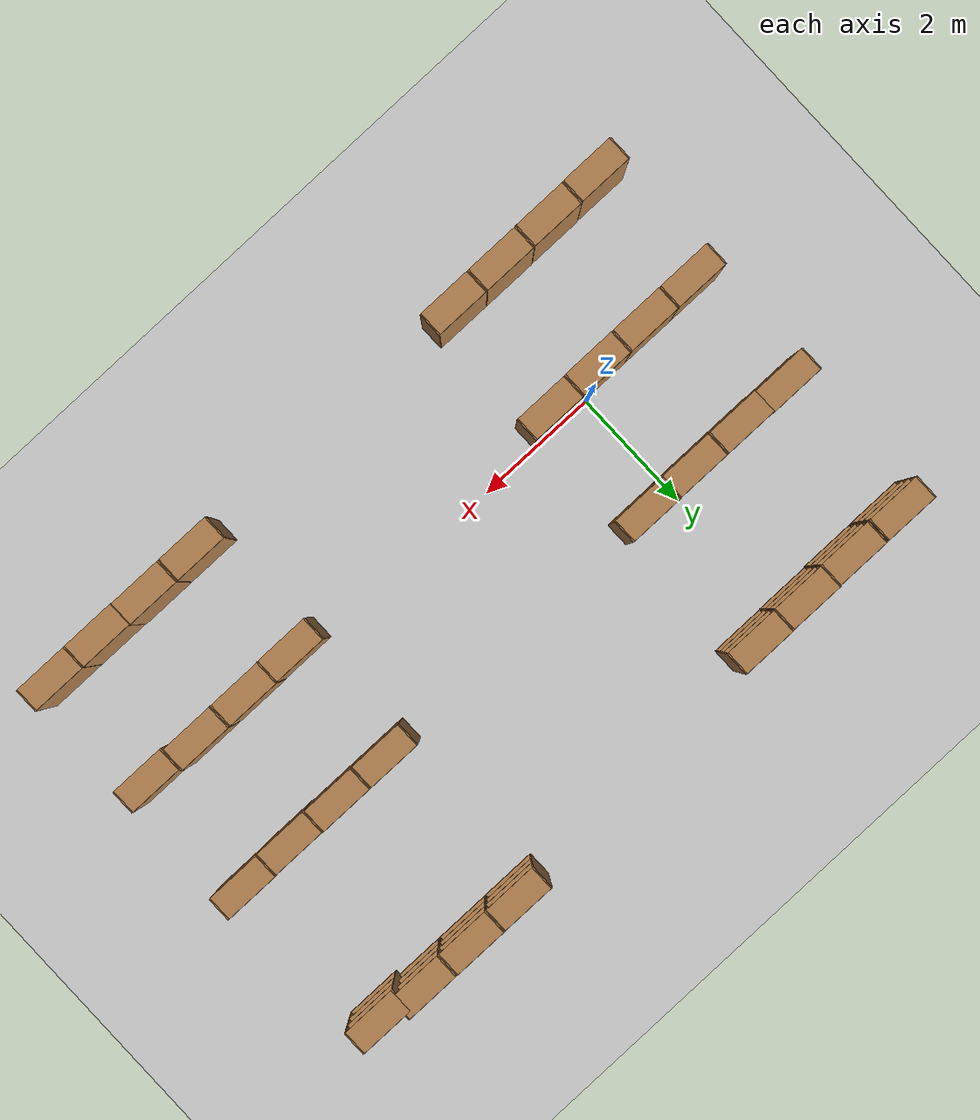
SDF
<sdf version="1.7">
 <world name="default">
  <light name="sun" type="directional">
   <pose>0 0 10 0 -0 0</pose>
   <diffuse>0.8 0.8 0.8 1</diffuse>
   <specular>0.2 0.2 0.2 1</specular>
   <attenuation>
    <range>1000</range>
    <constant>0.9</constant>
    <linear>0.01</linear>
    <quadratic>0.001</quadratic>
   </attenuation>
   <direction>-0.5 0.1 -0.9</direction>
   <spot><inner_angle>0</inner_angle><outer_angle>0</outer_angle><falloff>0</falloff></spot>
  </light>
  <model name="ground_plane">
   <static>1</static>
   <link name="link">
    <collision name="collision">
     <geometry><plane><normal>0 0 1</normal><size>100 100</size></plane></geometry>
     <surface>
      <contact><collide_bitmask>65535</collide_bitmask></contact>
      <friction><ode><mu>100</mu><mu2>50</mu2></ode></friction>
     </surface>
    </collision>
    <visual name="visual">
     <cast_shadows>0</cast_shadows>
     <geometry><plane><normal>0 0 1</normal><size>100 100</size></plane></geometry>
     <material>
      <script><uri>file://media/materials/scripts/gazebo.material</uri><name>Gazebo/Grey</name></script>
     </material>
    </visual>
   </link>
  </model>
  <gravity>0 0 -9.8</gravity>
  <magnetic_field>6e-06 2.3e-05 -4.2e-05</magnetic_field>
  <atmosphere type="adiabatic"/>
  <physics type="ode">
   <max_step_size>0.001</max_step_size>
   <real_time_factor>1</real_time_factor>
   <real_time_update_rate>1000</real_time_update_rate>
  </physics>
  <scene><ambient>0.4 0.4 0.4 1</ambient><background>0.7 0.7 0.7 1</background><shadows>1</shadows></scene>
  <spherical_coordinates>
   <surface_model>EARTH_WGS84</surface_model>
   <latitude_deg>0</latitude_deg>
   <longitude_deg>0</longitude_deg>
   <elevation>0</elevation>
   <heading_deg>0</heading_deg>
  </spherical_coordinates>
  <model name="bookshelf">
   <static>1</static>
   <link name="link">
    <inertial><mass>1</mass></inertial>
    <collision name="back">
     <pose>0 0.005 0.6 0 -0 0</pose>
     <geometry><box><size>0.9 0.01 1.2</size></box></geometry>
    </collision>
    <visual name="visual1">
     <pose>0 0.005 0.6 0 -0 0</pose>
     <geometry><box><size>0.9 0.01 1.2</size></box></geometry>
     <material>
      <script><uri>file://media/materials/scripts/gazebo.material</uri><name>Gazebo/Wood</name></script>
     </material>
    </visual>
    <collision name="left_side">
     <pose>0.45 -0.195 0.6 0 -0 0</pose>
     <geometry><box><size>0.02 0.4 1.2</size></box></geometry>
    </collision>
    <visual name="visual2">
     <pose>0.45 -0.195 0.6 0 -0 0</pose>
     <geometry><box><size>0.02 0.4 1.2</size></box></geometry>
     <material>
      <script><uri>file://media/materials/scripts/gazebo.material</uri><name>Gazebo/Wood</name></script>
     </material>
    </visual>
    <collision name="right_side">
     <pose>-0.45 -0.195 0.6 0 -0 0</pose>
     <geometry><box><size>0.02 0.4 1.2</size></box></geometry>
    </collision>
    <visual name="visual3">
     <pose>-0.45 -0.195 0.6 0 -0 0</pose>
     <geometry><box><size>0.02 0.4 1.2</size></box></geometry>
     <material>
      <script><uri>file://media/materials/scripts/gazebo.material</uri><name>Gazebo/Wood</name></script>
     </material>
    </visual>
    <collision name="bottom">
     <pose>0 -0.195 0.03 0 -0 0</pose>
     <geometry><box><size>0.88 0.4 0.06</size></box></geometry>
    </collision>
    <visual name="visual4">
     <pose>0 -0.195 0.03 0 -0 0</pose>
     <geometry><box><size>0.88 0.4 0.06</size></box></geometry>
     <material>
      <script><uri>file://media/materials/scripts/gazebo.material</uri><name>Gazebo/Wood</name></script>
     </material>
    </visual>
    <collision name="top">
     <pose>0 -0.195 1.19 0 -0 0</pose>
     <geometry><box><size>0.88 0.4 0.02</size></box></geometry>
    </collision>
    <visual name="visual5">
     <pose>0 -0.195 1.19 0 -0 0</pose>
     <geometry><box><size>0.88 0.4 0.02</size></box></geometry>
     <material>
      <script><uri>file://media/materials/scripts/gazebo.material</uri><name>Gazebo/Wood</name></script>
     </material>
    </visual>
    <collision name="low_shelf">
     <pose>0 -0.195 0.43 0 -0 0</pose>
     <geometry><box><size>0.88 0.4 0.02</size></box></geometry>
    </collision>
    <visual name="visual6">
     <pose>0 -0.195 0.43 0 -0 0</pose>
     <geometry><box><size>0.88 0.4 0.02</size></box></geometry>
     <material>
      <script><uri>file://media/materials/scripts/gazebo.material</uri><name>Gazebo/Wood</name></script>
     </material>
    </visual>
    <collision name="high_shelf">
     <pose>0 -0.195 0.8 0 -0 0</pose>
     <geometry><box><size>0.88 0.4 0.02</size></box></geometry>
    </collision>
    <visual name="visual7">
     <pose>0 -0.195 0.8 0 -0 0</pose>
     <geometry><box><size>0.88 0.4 0.02</size></box></geometry>
     <material>
      <script><uri>file://media/materials/scripts/gazebo.material</uri><name>Gazebo/Wood</name></script>
     </material>
    </visual>
   </link>
   <pose>-2.10101 4.39062 0 0 -0 0</pose>
  </model>
  <model name="bookshelf_clone">
   <static>1</static>
   <link name="link">
    <inertial><mass>1</mass></inertial>
    <collision name="back">
     <pose>0 0.005 0.6 0 -0 0</pose>
     <geometry><box><size>0.9 0.01 1.2</size></box></geometry>
    </collision>
    <visual name="visual1">
     <pose>0 0.005 0.6 0 -0 0</pose>
     <geometry><box><size>0.9 0.01 1.2</size></box></geometry>
     <material>
      <script><uri>file://media/materials/scripts/gazebo.material</uri><name>Gazebo/Wood</name></script>
     </material>
    </visual>
    <collision name="left_side">
     <pose>0.45 -0.195 0.6 0 -0 0</pose>
     <geometry><box><size>0.02 0.4 1.2</size></box></geometry>
    </collision>
    <visual name="visual2">
     <pose>0.45 -0.195 0.6 0 -0 0</pose>
     <geometry><box><size>0.02 0.4 1.2</size></box></geometry>
     <material>
      <script><uri>file://media/materials/scripts/gazebo.material</uri><name>Gazebo/Wood</name></script>
     </material>
    </visual>
    <collision name="right_side">
     <pose>-0.45 -0.195 0.6 0 -0 0</pose>
     <geometry><box><size>0.02 0.4 1.2</size></box></geometry>
    </collision>
    <visual name="visual3">
     <pose>-0.45 -0.195 0.6 0 -0 0</pose>
     <geometry><box><size>0.02 0.4 1.2</size></box></geometry>
     <material>
      <script><uri>file://media/materials/scripts/gazebo.material</uri><name>Gazebo/Wood</name></script>
     </material>
    </visual>
    <collision name="bottom">
     <pose>0 -0.195 0.03 0 -0 0</pose>
     <geometry><box><size>0.88 0.4 0.06</size></box></geometry>
    </collision>
    <visual name="visual4">
     <pose>0 -0.195 0.03 0 -0 0</pose>
     <geometry><box><size>0.88 0.4 0.06</size></box></geometry>
     <material>
      <script><uri>file://media/materials/scripts/gazebo.material</uri><name>Gazebo/Wood</name></script>
     </material>
    </visual>
    <collision name="top">
     <pose>0 -0.195 1.19 0 -0 0</pose>
     <geometry><box><size>0.88 0.4 0.02</size></box></geometry>
    </collision>
    <visual name="visual5">
     <pose>0 -0.195 1.19 0 -0 0</pose>
     <geometry><box><size>0.88 0.4 0.02</size></box></geometry>
     <material>
      <script><uri>file://media/materials/scripts/gazebo.material</uri><name>Gazebo/Wood</name></script>
     </material>
    </visual>
    <collision name="low_shelf">
     <pose>0 -0.195 0.43 0 -0 0</pose>
     <geometry><box><size>0.88 0.4 0.02</size></box></geometry>
    </collision>
    <visual name="visual6">
     <pose>0 -0.195 0.43 0 -0 0</pose>
     <geometry><box><size>0.88 0.4 0.02</size></box></geometry>
     <material>
      <script><uri>file://media/materials/scripts/gazebo.material</uri><name>Gazebo/Wood</name></script>
     </material>
    </visual>
    <collision name="high_shelf">
     <pose>0 -0.195 0.8 0 -0 0</pose>
     <geometry><box><size>0.88 0.4 0.02</size></box></geometry>
    </collision>
    <visual name="visual7">
     <pose>0 -0.195 0.8 0 -0 0</pose>
     <geometry><box><size>0.88 0.4 0.02</size></box></geometry>
     <material>
      <script><uri>file://media/materials/scripts/gazebo.material</uri><name>Gazebo/Wood</name></script>
     </material>
    </visual>
   </link>
   <pose>-1.16841 4.39364 0 0 -0 0</pose>
  </model>
  <model name="bookshelf_clone_0">
   <static>1</static>
   <link name="link">
    <inertial><mass>1</mass></inertial>
    <collision name="back">
     <pose>0 0.005 0.6 0 -0 0</pose>
     <geometry><box><size>0.9 0.01 1.2</size></box></geometry>
    </collision>
    <visual name="visual1">
     <pose>0 0.005 0.6 0 -0 0</pose>
     <geometry><box><size>0.9 0.01 1.2</size></box></geometry>
     <material>
      <script><uri>file://media/materials/scripts/gazebo.material</uri><name>Gazebo/Wood</name></script>
     </material>
    </visual>
    <collision name="left_side">
     <pose>0.45 -0.195 0.6 0 -0 0</pose>
     <geometry><box><size>0.02 0.4 1.2</size></box></geometry>
    </collision>
    <visual name="visual2">
     <pose>0.45 -0.195 0.6 0 -0 0</pose>
     <geometry><box><size>0.02 0.4 1.2</size></box></geometry>
     <material>
      <script><uri>file://media/materials/scripts/gazebo.material</uri><name>Gazebo/Wood</name></script>
     </material>
    </visual>
    <collision name="right_side">
     <pose>-0.45 -0.195 0.6 0 -0 0</pose>
     <geometry><box><size>0.02 0.4 1.2</size></box></geometry>
    </collision>
    <visual name="visual3">
     <pose>-0.45 -0.195 0.6 0 -0 0</pose>
     <geometry><box><size>0.02 0.4 1.2</size></box></geometry>
     <material>
      <script><uri>file://media/materials/scripts/gazebo.material</uri><name>Gazebo/Wood</name></script>
     </material>
    </visual>
    <collision name="bottom">
     <pose>0 -0.195 0.03 0 -0 0</pose>
     <geometry><box><size>0.88 0.4 0.06</size></box></geometry>
    </collision>
    <visual name="visual4">
     <pose>0 -0.195 0.03 0 -0 0</pose>
     <geometry><box><size>0.88 0.4 0.06</size></box></geometry>
     <material>
      <script><uri>file://media/materials/scripts/gazebo.material</uri><name>Gazebo/Wood</name></script>
     </material>
    </visual>
    <collision name="top">
     <pose>0 -0.195 1.19 0 -0 0</pose>
     <geometry><box><size>0.88 0.4 0.02</size></box></geometry>
    </collision>
    <visual name="visual5">
     <pose>0 -0.195 1.19 0 -0 0</pose>
     <geometry><box><size>0.88 0.4 0.02</size></box></geometry>
     <material>
      <script><uri>file://media/materials/scripts/gazebo.material</uri><name>Gazebo/Wood</name></script>
     </material>
    </visual>
    <collision name="low_shelf">
     <pose>0 -0.195 0.43 0 -0 0</pose>
     <geometry><box><size>0.88 0.4 0.02</size></box></geometry>
    </collision>
    <visual name="visual6">
     <pose>0 -0.195 0.43 0 -0 0</pose>
     <geometry><box><size>0.88 0.4 0.02</size></box></geometry>
     <material>
      <script><uri>file://media/materials/scripts/gazebo.material</uri><name>Gazebo/Wood</name></script>
     </material>
    </visual>
    <collision name="high_shelf">
     <pose>0 -0.195 0.8 0 -0 0</pose>
     <geometry><box><size>0.88 0.4 0.02</size></box></geometry>
    </collision>
    <visual name="visual7">
     <pose>0 -0.195 0.8 0 -0 0</pose>
     <geometry><box><size>0.88 0.4 0.02</size></box></geometry>
     <material>
      <script><uri>file://media/materials/scripts/gazebo.material</uri><name>Gazebo/Wood</name></script>
     </material>
    </visual>
   </link>
   <pose>-0.260322 4.40526 0 0 -0 0</pose>
  </model>
  <model name="bookshelf_clone_1">
   <static>1</static>
   <link name="link">
    <inertial><mass>1</mass></inertial>
    <collision name="back">
     <pose>0 0.005 0.6 0 -0 0</pose>
     <geometry><box><size>0.9 0.01 1.2</size></box></geometry>
    </collision>
    <visual name="visual1">
     <pose>0 0.005 0.6 0 -0 0</pose>
     <geometry><box><size>0.9 0.01 1.2</size></box></geometry>
     <material>
      <script><uri>file://media/materials/scripts/gazebo.material</uri><name>Gazebo/Wood</name></script>
     </material>
    </visual>
    <collision name="left_side">
     <pose>0.45 -0.195 0.6 0 -0 0</pose>
     <geometry><box><size>0.02 0.4 1.2</size></box></geometry>
    </collision>
    <visual name="visual2">
     <pose>0.45 -0.195 0.6 0 -0 0</pose>
     <geometry><box><size>0.02 0.4 1.2</size></box></geometry>
     <material>
      <script><uri>file://media/materials/scripts/gazebo.material</uri><name>Gazebo/Wood</name></script>
     </material>
    </visual>
    <collision name="right_side">
     <pose>-0.45 -0.195 0.6 0 -0 0</pose>
     <geometry><box><size>0.02 0.4 1.2</size></box></geometry>
    </collision>
    <visual name="visual3">
     <pose>-0.45 -0.195 0.6 0 -0 0</pose>
     <geometry><box><size>0.02 0.4 1.2</size></box></geometry>
     <material>
      <script><uri>file://media/materials/scripts/gazebo.material</uri><name>Gazebo/Wood</name></script>
     </material>
    </visual>
    <collision name="bottom">
     <pose>0 -0.195 0.03 0 -0 0</pose>
     <geometry><box><size>0.88 0.4 0.06</size></box></geometry>
    </collision>
    <visual name="visual4">
     <pose>0 -0.195 0.03 0 -0 0</pose>
     <geometry><box><size>0.88 0.4 0.06</size></box></geometry>
     <material>
      <script><uri>file://media/materials/scripts/gazebo.material</uri><name>Gazebo/Wood</name></script>
     </material>
    </visual>
    <collision name="top">
     <pose>0 -0.195 1.19 0 -0 0</pose>
     <geometry><box><size>0.88 0.4 0.02</size></box></geometry>
    </collision>
    <visual name="visual5">
     <pose>0 -0.195 1.19 0 -0 0</pose>
     <geometry><box><size>0.88 0.4 0.02</size></box></geometry>
     <material>
      <script><uri>file://media/materials/scripts/gazebo.material</uri><name>Gazebo/Wood</name></script>
     </material>
    </visual>
    <collision name="low_shelf">
     <pose>0 -0.195 0.43 0 -0 0</pose>
     <geometry><box><size>0.88 0.4 0.02</size></box></geometry>
    </collision>
    <visual name="visual6">
     <pose>0 -0.195 0.43 0 -0 0</pose>
     <geometry><box><size>0.88 0.4 0.02</size></box></geometry>
     <material>
      <script><uri>file://media/materials/scripts/gazebo.material</uri><name>Gazebo/Wood</name></script>
     </material>
    </visual>
    <collision name="high_shelf">
     <pose>0 -0.195 0.8 0 -0 0</pose>
     <geometry><box><size>0.88 0.4 0.02</size></box></geometry>
    </collision>
    <visual name="visual7">
     <pose>0 -0.195 0.8 0 -0 0</pose>
     <geometry><box><size>0.88 0.4 0.02</size></box></geometry>
     <material>
      <script><uri>file://media/materials/scripts/gazebo.material</uri><name>Gazebo/Wood</name></script>
     </material>
    </visual>
   </link>
   <pose>0.651315 4.41227 0 0 -0 0</pose>
  </model>
  <model name="bookshelf_clone_2">
   <static>1</static>
   <link name="link">
    <inertial><mass>1</mass></inertial>
    <collision name="back">
     <pose>0 0.005 0.6 0 -0 0</pose>
     <geometry><box><size>0.9 0.01 1.2</size></box></geometry>
    </collision>
    <visual name="visual1">
     <pose>0 0.005 0.6 0 -0 0</pose>
     <geometry><box><size>0.9 0.01 1.2</size></box></geometry>
     <material>
      <script><uri>file://media/materials/scripts/gazebo.material</uri><name>Gazebo/Wood</name></script>
     </material>
    </visual>
    <collision name="left_side">
     <pose>0.45 -0.195 0.6 0 -0 0</pose>
     <geometry><box><size>0.02 0.4 1.2</size></box></geometry>
    </collision>
    <visual name="visual2">
     <pose>0.45 -0.195 0.6 0 -0 0</pose>
     <geometry><box><size>0.02 0.4 1.2</size></box></geometry>
     <material>
      <script><uri>file://media/materials/scripts/gazebo.material</uri><name>Gazebo/Wood</name></script>
     </material>
    </visual>
    <collision name="right_side">
     <pose>-0.45 -0.195 0.6 0 -0 0</pose>
     <geometry><box><size>0.02 0.4 1.2</size></box></geometry>
    </collision>
    <visual name="visual3">
     <pose>-0.45 -0.195 0.6 0 -0 0</pose>
     <geometry><box><size>0.02 0.4 1.2</size></box></geometry>
     <material>
      <script><uri>file://media/materials/scripts/gazebo.material</uri><name>Gazebo/Wood</name></script>
     </material>
    </visual>
    <collision name="bottom">
     <pose>0 -0.195 0.03 0 -0 0</pose>
     <geometry><box><size>0.88 0.4 0.06</size></box></geometry>
    </collision>
    <visual name="visual4">
     <pose>0 -0.195 0.03 0 -0 0</pose>
     <geometry><box><size>0.88 0.4 0.06</size></box></geometry>
     <material>
      <script><uri>file://media/materials/scripts/gazebo.material</uri><name>Gazebo/Wood</name></script>
     </material>
    </visual>
    <collision name="top">
     <pose>0 -0.195 1.19 0 -0 0</pose>
     <geometry><box><size>0.88 0.4 0.02</size></box></geometry>
    </collision>
    <visual name="visual5">
     <pose>0 -0.195 1.19 0 -0 0</pose>
     <geometry><box><size>0.88 0.4 0.02</size></box></geometry>
     <material>
      <script><uri>file://media/materials/scripts/gazebo.material</uri><name>Gazebo/Wood</name></script>
     </material>
    </visual>
    <collision name="low_shelf">
     <pose>0 -0.195 0.43 0 -0 0</pose>
     <geometry><box><size>0.88 0.4 0.02</size></box></geometry>
    </collision>
    <visual name="visual6">
     <pose>0 -0.195 0.43 0 -0 0</pose>
     <geometry><box><size>0.88 0.4 0.02</size></box></geometry>
     <material>
      <script><uri>file://media/materials/scripts/gazebo.material</uri><name>Gazebo/Wood</name></script>
     </material>
    </visual>
    <collision name="high_shelf">
     <pose>0 -0.195 0.8 0 -0 0</pose>
     <geometry><box><size>0.88 0.4 0.02</size></box></geometry>
    </collision>
    <visual name="visual7">
     <pose>0 -0.195 0.8 0 -0 0</pose>
     <geometry><box><size>0.88 0.4 0.02</size></box></geometry>
     <material>
      <script><uri>file://media/materials/scripts/gazebo.material</uri><name>Gazebo/Wood</name></script>
     </material>
    </visual>
   </link>
   <pose>-2.14435 1.96443 0 0 -0 0</pose>
  </model>
  <model name="bookshelf_clone_3">
   <static>1</static>
   <link name="link">
    <inertial><mass>1</mass></inertial>
    <collision name="back">
     <pose>0 0.005 0.6 0 -0 0</pose>
     <geometry><box><size>0.9 0.01 1.2</size></box></geometry>
    </collision>
    <visual name="visual1">
     <pose>0 0.005 0.6 0 -0 0</pose>
     <geometry><box><size>0.9 0.01 1.2</size></box></geometry>
     <material>
      <script><uri>file://media/materials/scripts/gazebo.material</uri><name>Gazebo/Wood</name></script>
     </material>
    </visual>
    <collision name="left_side">
     <pose>0.45 -0.195 0.6 0 -0 0</pose>
     <geometry><box><size>0.02 0.4 1.2</size></box></geometry>
    </collision>
    <visual name="visual2">
     <pose>0.45 -0.195 0.6 0 -0 0</pose>
     <geometry><box><size>0.02 0.4 1.2</size></box></geometry>
     <material>
      <script><uri>file://media/materials/scripts/gazebo.material</uri><name>Gazebo/Wood</name></script>
     </material>
    </visual>
    <collision name="right_side">
     <pose>-0.45 -0.195 0.6 0 -0 0</pose>
     <geometry><box><size>0.02 0.4 1.2</size></box></geometry>
    </collision>
    <visual name="visual3">
     <pose>-0.45 -0.195 0.6 0 -0 0</pose>
     <geometry><box><size>0.02 0.4 1.2</size></box></geometry>
     <material>
      <script><uri>file://media/materials/scripts/gazebo.material</uri><name>Gazebo/Wood</name></script>
     </material>
    </visual>
    <collision name="bottom">
     <pose>0 -0.195 0.03 0 -0 0</pose>
     <geometry><box><size>0.88 0.4 0.06</size></box></geometry>
    </collision>
    <visual name="visual4">
     <pose>0 -0.195 0.03 0 -0 0</pose>
     <geometry><box><size>0.88 0.4 0.06</size></box></geometry>
     <material>
      <script><uri>file://media/materials/scripts/gazebo.material</uri><name>Gazebo/Wood</name></script>
     </material>
    </visual>
    <collision name="top">
     <pose>0 -0.195 1.19 0 -0 0</pose>
     <geometry><box><size>0.88 0.4 0.02</size></box></geometry>
    </collision>
    <visual name="visual5">
     <pose>0 -0.195 1.19 0 -0 0</pose>
     <geometry><box><size>0.88 0.4 0.02</size></box></geometry>
     <material>
      <script><uri>file://media/materials/scripts/gazebo.material</uri><name>Gazebo/Wood</name></script>
     </material>
    </visual>
    <collision name="low_shelf">
     <pose>0 -0.195 0.43 0 -0 0</pose>
     <geometry><box><size>0.88 0.4 0.02</size></box></geometry>
    </collision>
    <visual name="visual6">
     <pose>0 -0.195 0.43 0 -0 0</pose>
     <geometry><box><size>0.88 0.4 0.02</size></box></geometry>
     <material>
      <script><uri>file://media/materials/scripts/gazebo.material</uri><name>Gazebo/Wood</name></script>
     </material>
    </visual>
    <collision name="high_shelf">
     <pose>0 -0.195 0.8 0 -0 0</pose>
     <geometry><box><size>0.88 0.4 0.02</size></box></geometry>
    </collision>
    <visual name="visual7">
     <pose>0 -0.195 0.8 0 -0 0</pose>
     <geometry><box><size>0.88 0.4 0.02</size></box></geometry>
     <material>
      <script><uri>file://media/materials/scripts/gazebo.material</uri><name>Gazebo/Wood</name></script>
     </material>
    </visual>
   </link>
   <pose>-1.2759 1.95521 0 0 -0 0</pose>
  </model>
  <model name="bookshelf_clone_4">
   <static>1</static>
   <link name="link">
    <inertial><mass>1</mass></inertial>
    <collision name="back">
     <pose>0 0.005 0.6 0 -0 0</pose>
     <geometry><box><size>0.9 0.01 1.2</size></box></geometry>
    </collision>
    <visual name="visual1">
     <pose>0 0.005 0.6 0 -0 0</pose>
     <geometry><box><size>0.9 0.01 1.2</size></box></geometry>
     <material>
      <script><uri>file://media/materials/scripts/gazebo.material</uri><name>Gazebo/Wood</name></script>
     </material>
    </visual>
    <collision name="left_side">
     <pose>0.45 -0.195 0.6 0 -0 0</pose>
     <geometry><box><size>0.02 0.4 1.2</size></box></geometry>
    </collision>
    <visual name="visual2">
     <pose>0.45 -0.195 0.6 0 -0 0</pose>
     <geometry><box><size>0.02 0.4 1.2</size></box></geometry>
     <material>
      <script><uri>file://media/materials/scripts/gazebo.material</uri><name>Gazebo/Wood</name></script>
     </material>
    </visual>
    <collision name="right_side">
     <pose>-0.45 -0.195 0.6 0 -0 0</pose>
     <geometry><box><size>0.02 0.4 1.2</size></box></geometry>
    </collision>
    <visual name="visual3">
     <pose>-0.45 -0.195 0.6 0 -0 0</pose>
     <geometry><box><size>0.02 0.4 1.2</size></box></geometry>
     <material>
      <script><uri>file://media/materials/scripts/gazebo.material</uri><name>Gazebo/Wood</name></script>
     </material>
    </visual>
    <collision name="bottom">
     <pose>0 -0.195 0.03 0 -0 0</pose>
     <geometry><box><size>0.88 0.4 0.06</size></box></geometry>
    </collision>
    <visual name="visual4">
     <pose>0 -0.195 0.03 0 -0 0</pose>
     <geometry><box><size>0.88 0.4 0.06</size></box></geometry>
     <material>
      <script><uri>file://media/materials/scripts/gazebo.material</uri><name>Gazebo/Wood</name></script>
     </material>
    </visual>
    <collision name="top">
     <pose>0 -0.195 1.19 0 -0 0</pose>
     <geometry><box><size>0.88 0.4 0.02</size></box></geometry>
    </collision>
    <visual name="visual5">
     <pose>0 -0.195 1.19 0 -0 0</pose>
     <geometry><box><size>0.88 0.4 0.02</size></box></geometry>
     <material>
      <script><uri>file://media/materials/scripts/gazebo.material</uri><name>Gazebo/Wood</name></script>
     </material>
    </visual>
    <collision name="low_shelf">
     <pose>0 -0.195 0.43 0 -0 0</pose>
     <geometry><box><size>0.88 0.4 0.02</size></box></geometry>
    </collision>
    <visual name="visual6">
     <pose>0 -0.195 0.43 0 -0 0</pose>
     <geometry><box><size>0.88 0.4 0.02</size></box></geometry>
     <material>
      <script><uri>file://media/materials/scripts/gazebo.material</uri><name>Gazebo/Wood</name></script>
     </material>
    </visual>
    <collision name="high_shelf">
     <pose>0 -0.195 0.8 0 -0 0</pose>
     <geometry><box><size>0.88 0.4 0.02</size></box></geometry>
    </collision>
    <visual name="visual7">
     <pose>0 -0.195 0.8 0 -0 0</pose>
     <geometry><box><size>0.88 0.4 0.02</size></box></geometry>
     <material>
      <script><uri>file://media/materials/scripts/gazebo.material</uri><name>Gazebo/Wood</name></script>
     </material>
    </visual>
   </link>
   <pose>-0.361156 1.95511 0 0 -0 0</pose>
  </model>
  <model name="bookshelf_clone_5">
   <static>1</static>
   <link name="link">
    <inertial><mass>1</mass></inertial>
    <collision name="back">
     <pose>0 0.005 0.6 0 -0 0</pose>
     <geometry><box><size>0.9 0.01 1.2</size></box></geometry>
    </collision>
    <visual name="visual1">
     <pose>0 0.005 0.6 0 -0 0</pose>
     <geometry><box><size>0.9 0.01 1.2</size></box></geometry>
     <material>
      <script><uri>file://media/materials/scripts/gazebo.material</uri><name>Gazebo/Wood</name></script>
     </material>
    </visual>
    <collision name="left_side">
     <pose>0.45 -0.195 0.6 0 -0 0</pose>
     <geometry><box><size>0.02 0.4 1.2</size></box></geometry>
    </collision>
    <visual name="visual2">
     <pose>0.45 -0.195 0.6 0 -0 0</pose>
     <geometry><box><size>0.02 0.4 1.2</size></box></geometry>
     <material>
      <script><uri>file://media/materials/scripts/gazebo.material</uri><name>Gazebo/Wood</name></script>
     </material>
    </visual>
    <collision name="right_side">
     <pose>-0.45 -0.195 0.6 0 -0 0</pose>
     <geometry><box><size>0.02 0.4 1.2</size></box></geometry>
    </collision>
    <visual name="visual3">
     <pose>-0.45 -0.195 0.6 0 -0 0</pose>
     <geometry><box><size>0.02 0.4 1.2</size></box></geometry>
     <material>
      <script><uri>file://media/materials/scripts/gazebo.material</uri><name>Gazebo/Wood</name></script>
     </material>
    </visual>
    <collision name="bottom">
     <pose>0 -0.195 0.03 0 -0 0</pose>
     <geometry><box><size>0.88 0.4 0.06</size></box></geometry>
    </collision>
    <visual name="visual4">
     <pose>0 -0.195 0.03 0 -0 0</pose>
     <geometry><box><size>0.88 0.4 0.06</size></box></geometry>
     <material>
      <script><uri>file://media/materials/scripts/gazebo.material</uri><name>Gazebo/Wood</name></script>
     </material>
    </visual>
    <collision name="top">
     <pose>0 -0.195 1.19 0 -0 0</pose>
     <geometry><box><size>0.88 0.4 0.02</size></box></geometry>
    </collision>
    <visual name="visual5">
     <pose>0 -0.195 1.19 0 -0 0</pose>
     <geometry><box><size>0.88 0.4 0.02</size></box></geometry>
     <material>
      <script><uri>file://media/materials/scripts/gazebo.material</uri><name>Gazebo/Wood</name></script>
     </material>
    </visual>
    <collision name="low_shelf">
     <pose>0 -0.195 0.43 0 -0 0</pose>
     <geometry><box><size>0.88 0.4 0.02</size></box></geometry>
    </collision>
    <visual name="visual6">
     <pose>0 -0.195 0.43 0 -0 0</pose>
     <geometry><box><size>0.88 0.4 0.02</size></box></geometry>
     <material>
      <script><uri>file://media/materials/scripts/gazebo.material</uri><name>Gazebo/Wood</name></script>
     </material>
    </visual>
    <collision name="high_shelf">
     <pose>0 -0.195 0.8 0 -0 0</pose>
     <geometry><box><size>0.88 0.4 0.02</size></box></geometry>
    </collision>
    <visual name="visual7">
     <pose>0 -0.195 0.8 0 -0 0</pose>
     <geometry><box><size>0.88 0.4 0.02</size></box></geometry>
     <material>
      <script><uri>file://media/materials/scripts/gazebo.material</uri><name>Gazebo/Wood</name></script>
     </material>
    </visual>
   </link>
   <pose>0.550206 1.96202 0 0 -0 0</pose>
  </model>
  <model name="bookshelf_clone_6">
   <static>1</static>
   <link name="link">
    <inertial><mass>1</mass></inertial>
    <collision name="back">
     <pose>0 0.005 0.6 0 -0 0</pose>
     <geometry><box><size>0.9 0.01 1.2</size></box></geometry>
    </collision>
    <visual name="visual1">
     <pose>0 0.005 0.6 0 -0 0</pose>
     <geometry><box><size>0.9 0.01 1.2</size></box></geometry>
     <material>
      <script><uri>file://media/materials/scripts/gazebo.material</uri><name>Gazebo/Wood</name></script>
     </material>
    </visual>
    <collision name="left_side">
     <pose>0.45 -0.195 0.6 0 -0 0</pose>
     <geometry><box><size>0.02 0.4 1.2</size></box></geometry>
    </collision>
    <visual name="visual2">
     <pose>0.45 -0.195 0.6 0 -0 0</pose>
     <geometry><box><size>0.02 0.4 1.2</size></box></geometry>
     <material>
      <script><uri>file://media/materials/scripts/gazebo.material</uri><name>Gazebo/Wood</name></script>
     </material>
    </visual>
    <collision name="right_side">
     <pose>-0.45 -0.195 0.6 0 -0 0</pose>
     <geometry><box><size>0.02 0.4 1.2</size></box></geometry>
    </collision>
    <visual name="visual3">
     <pose>-0.45 -0.195 0.6 0 -0 0</pose>
     <geometry><box><size>0.02 0.4 1.2</size></box></geometry>
     <material>
      <script><uri>file://media/materials/scripts/gazebo.material</uri><name>Gazebo/Wood</name></script>
     </material>
    </visual>
    <collision name="bottom">
     <pose>0 -0.195 0.03 0 -0 0</pose>
     <geometry><box><size>0.88 0.4 0.06</size></box></geometry>
    </collision>
    <visual name="visual4">
     <pose>0 -0.195 0.03 0 -0 0</pose>
     <geometry><box><size>0.88 0.4 0.06</size></box></geometry>
     <material>
      <script><uri>file://media/materials/scripts/gazebo.material</uri><name>Gazebo/Wood</name></script>
     </material>
    </visual>
    <collision name="top">
     <pose>0 -0.195 1.19 0 -0 0</pose>
     <geometry><box><size>0.88 0.4 0.02</size></box></geometry>
    </collision>
    <visual name="visual5">
     <pose>0 -0.195 1.19 0 -0 0</pose>
     <geometry><box><size>0.88 0.4 0.02</size></box></geometry>
     <material>
      <script><uri>file://media/materials/scripts/gazebo.material</uri><name>Gazebo/Wood</name></script>
     </material>
    </visual>
    <collision name="low_shelf">
     <pose>0 -0.195 0.43 0 -0 0</pose>
     <geometry><box><size>0.88 0.4 0.02</size></box></geometry>
    </collision>
    <visual name="visual6">
     <pose>0 -0.195 0.43 0 -0 0</pose>
     <geometry><box><size>0.88 0.4 0.02</size></box></geometry>
     <material>
      <script><uri>file://media/materials/scripts/gazebo.material</uri><name>Gazebo/Wood</name></script>
     </material>
    </visual>
    <collision name="high_shelf">
     <pose>0 -0.195 0.8 0 -0 0</pose>
     <geometry><box><size>0.88 0.4 0.02</size></box></geometry>
    </collision>
    <visual name="visual7">
     <pose>0 -0.195 0.8 0 -0 0</pose>
     <geometry><box><size>0.88 0.4 0.02</size></box></geometry>
     <material>
      <script><uri>file://media/materials/scripts/gazebo.material</uri><name>Gazebo/Wood</name></script>
     </material>
    </visual>
   </link>
   <pose>-2.16744 -0.032572 0 0 -0 0</pose>
  </model>
  <model name="bookshelf_clone_7">
   <static>1</static>
   <link name="link">
    <inertial><mass>1</mass></inertial>
    <collision name="back">
     <pose>0 0.005 0.6 0 -0 0</pose>
     <geometry><box><size>0.9 0.01 1.2</size></box></geometry>
    </collision>
    <visual name="visual1">
     <pose>0 0.005 0.6 0 -0 0</pose>
     <geometry><box><size>0.9 0.01 1.2</size></box></geometry>
     <material>
      <script><uri>file://media/materials/scripts/gazebo.material</uri><name>Gazebo/Wood</name></script>
     </material>
    </visual>
    <collision name="left_side">
     <pose>0.45 -0.195 0.6 0 -0 0</pose>
     <geometry><box><size>0.02 0.4 1.2</size></box></geometry>
    </collision>
    <visual name="visual2">
     <pose>0.45 -0.195 0.6 0 -0 0</pose>
     <geometry><box><size>0.02 0.4 1.2</size></box></geometry>
     <material>
      <script><uri>file://media/materials/scripts/gazebo.material</uri><name>Gazebo/Wood</name></script>
     </material>
    </visual>
    <collision name="right_side">
     <pose>-0.45 -0.195 0.6 0 -0 0</pose>
     <geometry><box><size>0.02 0.4 1.2</size></box></geometry>
    </collision>
    <visual name="visual3">
     <pose>-0.45 -0.195 0.6 0 -0 0</pose>
     <geometry><box><size>0.02 0.4 1.2</size></box></geometry>
     <material>
      <script><uri>file://media/materials/scripts/gazebo.material</uri><name>Gazebo/Wood</name></script>
     </material>
    </visual>
    <collision name="bottom">
     <pose>0 -0.195 0.03 0 -0 0</pose>
     <geometry><box><size>0.88 0.4 0.06</size></box></geometry>
    </collision>
    <visual name="visual4">
     <pose>0 -0.195 0.03 0 -0 0</pose>
     <geometry><box><size>0.88 0.4 0.06</size></box></geometry>
     <material>
      <script><uri>file://media/materials/scripts/gazebo.material</uri><name>Gazebo/Wood</name></script>
     </material>
    </visual>
    <collision name="top">
     <pose>0 -0.195 1.19 0 -0 0</pose>
     <geometry><box><size>0.88 0.4 0.02</size></box></geometry>
    </collision>
    <visual name="visual5">
     <pose>0 -0.195 1.19 0 -0 0</pose>
     <geometry><box><size>0.88 0.4 0.02</size></box></geometry>
     <material>
      <script><uri>file://media/materials/scripts/gazebo.material</uri><name>Gazebo/Wood</name></script>
     </material>
    </visual>
    <collision name="low_shelf">
     <pose>0 -0.195 0.43 0 -0 0</pose>
     <geometry><box><size>0.88 0.4 0.02</size></box></geometry>
    </collision>
    <visual name="visual6">
     <pose>0 -0.195 0.43 0 -0 0</pose>
     <geometry><box><size>0.88 0.4 0.02</size></box></geometry>
     <material>
      <script><uri>file://media/materials/scripts/gazebo.material</uri><name>Gazebo/Wood</name></script>
     </material>
    </visual>
    <collision name="high_shelf">
     <pose>0 -0.195 0.8 0 -0 0</pose>
     <geometry><box><size>0.88 0.4 0.02</size></box></geometry>
    </collision>
    <visual name="visual7">
     <pose>0 -0.195 0.8 0 -0 0</pose>
     <geometry><box><size>0.88 0.4 0.02</size></box></geometry>
     <material>
      <script><uri>file://media/materials/scripts/gazebo.material</uri><name>Gazebo/Wood</name></script>
     </material>
    </visual>
   </link>
   <pose>-1.25423 -0.032337 0 0 -0 0</pose>
  </model>
  <model name="bookshelf_clone_8">
   <static>1</static>
   <link name="link">
    <inertial><mass>1</mass></inertial>
    <collision name="back">
     <pose>0 0.005 0.6 0 -0 0</pose>
     <geometry><box><size>0.9 0.01 1.2</size></box></geometry>
    </collision>
    <visual name="visual1">
     <pose>0 0.005 0.6 0 -0 0</pose>
     <geometry><box><size>0.9 0.01 1.2</size></box></geometry>
     <material>
      <script><uri>file://media/materials/scripts/gazebo.material</uri><name>Gazebo/Wood</name></script>
     </material>
    </visual>
    <collision name="left_side">
     <pose>0.45 -0.195 0.6 0 -0 0</pose>
     <geometry><box><size>0.02 0.4 1.2</size></box></geometry>
    </collision>
    <visual name="visual2">
     <pose>0.45 -0.195 0.6 0 -0 0</pose>
     <geometry><box><size>0.02 0.4 1.2</size></box></geometry>
     <material>
      <script><uri>file://media/materials/scripts/gazebo.material</uri><name>Gazebo/Wood</name></script>
     </material>
    </visual>
    <collision name="right_side">
     <pose>-0.45 -0.195 0.6 0 -0 0</pose>
     <geometry><box><size>0.02 0.4 1.2</size></box></geometry>
    </collision>
    <visual name="visual3">
     <pose>-0.45 -0.195 0.6 0 -0 0</pose>
     <geometry><box><size>0.02 0.4 1.2</size></box></geometry>
     <material>
      <script><uri>file://media/materials/scripts/gazebo.material</uri><name>Gazebo/Wood</name></script>
     </material>
    </visual>
    <collision name="bottom">
     <pose>0 -0.195 0.03 0 -0 0</pose>
     <geometry><box><size>0.88 0.4 0.06</size></box></geometry>
    </collision>
    <visual name="visual4">
     <pose>0 -0.195 0.03 0 -0 0</pose>
     <geometry><box><size>0.88 0.4 0.06</size></box></geometry>
     <material>
      <script><uri>file://media/materials/scripts/gazebo.material</uri><name>Gazebo/Wood</name></script>
     </material>
    </visual>
    <collision name="top">
     <pose>0 -0.195 1.19 0 -0 0</pose>
     <geometry><box><size>0.88 0.4 0.02</size></box></geometry>
    </collision>
    <visual name="visual5">
     <pose>0 -0.195 1.19 0 -0 0</pose>
     <geometry><box><size>0.88 0.4 0.02</size></box></geometry>
     <material>
      <script><uri>file://media/materials/scripts/gazebo.material</uri><name>Gazebo/Wood</name></script>
     </material>
    </visual>
    <collision name="low_shelf">
     <pose>0 -0.195 0.43 0 -0 0</pose>
     <geometry><box><size>0.88 0.4 0.02</size></box></geometry>
    </collision>
    <visual name="visual6">
     <pose>0 -0.195 0.43 0 -0 0</pose>
     <geometry><box><size>0.88 0.4 0.02</size></box></geometry>
     <material>
      <script><uri>file://media/materials/scripts/gazebo.material</uri><name>Gazebo/Wood</name></script>
     </material>
    </visual>
    <collision name="high_shelf">
     <pose>0 -0.195 0.8 0 -0 0</pose>
     <geometry><box><size>0.88 0.4 0.02</size></box></geometry>
    </collision>
    <visual name="visual7">
     <pose>0 -0.195 0.8 0 -0 0</pose>
     <geometry><box><size>0.88 0.4 0.02</size></box></geometry>
     <material>
      <script><uri>file://media/materials/scripts/gazebo.material</uri><name>Gazebo/Wood</name></script>
     </material>
    </visual>
   </link>
   <pose>-0.335957 -0.032337 0 0 -0 0</pose>
  </model>
  <model name="bookshelf_clone_9">
   <static>1</static>
   <link name="link">
    <inertial><mass>1</mass></inertial>
    <collision name="back">
     <pose>0 0.005 0.6 0 -0 0</pose>
     <geometry><box><size>0.9 0.01 1.2</size></box></geometry>
    </collision>
    <visual name="visual1">
     <pose>0 0.005 0.6 0 -0 0</pose>
     <geometry><box><size>0.9 0.01 1.2</size></box></geometry>
     <material>
      <script><uri>file://media/materials/scripts/gazebo.material</uri><name>Gazebo/Wood</name></script>
     </material>
    </visual>
    <collision name="left_side">
     <pose>0.45 -0.195 0.6 0 -0 0</pose>
     <geometry><box><size>0.02 0.4 1.2</size></box></geometry>
    </collision>
    <visual name="visual2">
     <pose>0.45 -0.195 0.6 0 -0 0</pose>
     <geometry><box><size>0.02 0.4 1.2</size></box></geometry>
     <material>
      <script><uri>file://media/materials/scripts/gazebo.material</uri><name>Gazebo/Wood</name></script>
     </material>
    </visual>
    <collision name="right_side">
     <pose>-0.45 -0.195 0.6 0 -0 0</pose>
     <geometry><box><size>0.02 0.4 1.2</size></box></geometry>
    </collision>
    <visual name="visual3">
     <pose>-0.45 -0.195 0.6 0 -0 0</pose>
     <geometry><box><size>0.02 0.4 1.2</size></box></geometry>
     <material>
      <script><uri>file://media/materials/scripts/gazebo.material</uri><name>Gazebo/Wood</name></script>
     </material>
    </visual>
    <collision name="bottom">
     <pose>0 -0.195 0.03 0 -0 0</pose>
     <geometry><box><size>0.88 0.4 0.06</size></box></geometry>
    </collision>
    <visual name="visual4">
     <pose>0 -0.195 0.03 0 -0 0</pose>
     <geometry><box><size>0.88 0.4 0.06</size></box></geometry>
     <material>
      <script><uri>file://media/materials/scripts/gazebo.material</uri><name>Gazebo/Wood</name></script>
     </material>
    </visual>
    <collision name="top">
     <pose>0 -0.195 1.19 0 -0 0</pose>
     <geometry><box><size>0.88 0.4 0.02</size></box></geometry>
    </collision>
    <visual name="visual5">
     <pose>0 -0.195 1.19 0 -0 0</pose>
     <geometry><box><size>0.88 0.4 0.02</size></box></geometry>
     <material>
      <script><uri>file://media/materials/scripts/gazebo.material</uri><name>Gazebo/Wood</name></script>
     </material>
    </visual>
    <collision name="low_shelf">
     <pose>0 -0.195 0.43 0 -0 0</pose>
     <geometry><box><size>0.88 0.4 0.02</size></box></geometry>
    </collision>
    <visual name="visual6">
     <pose>0 -0.195 0.43 0 -0 0</pose>
     <geometry><box><size>0.88 0.4 0.02</size></box></geometry>
     <material>
      <script><uri>file://media/materials/scripts/gazebo.material</uri><name>Gazebo/Wood</name></script>
     </material>
    </visual>
    <collision name="high_shelf">
     <pose>0 -0.195 0.8 0 -0 0</pose>
     <geometry><box><size>0.88 0.4 0.02</size></box></geometry>
    </collision>
    <visual name="visual7">
     <pose>0 -0.195 0.8 0 -0 0</pose>
     <geometry><box><size>0.88 0.4 0.02</size></box></geometry>
     <material>
      <script><uri>file://media/materials/scripts/gazebo.material</uri><name>Gazebo/Wood</name></script>
     </material>
    </visual>
   </link>
   <pose>0.583524 -0.025922 0 0 -0 0</pose>
  </model>
  <model name="bookshelf_clone_10">
   <static>1</static>
   <link name="link">
    <inertial><mass>1</mass></inertial>
    <collision name="back">
     <pose>0 0.005 0.6 0 -0 0</pose>
     <geometry><box><size>0.9 0.01 1.2</size></box></geometry>
    </collision>
    <visual name="visual1">
     <pose>0 0.005 0.6 0 -0 0</pose>
     <geometry><box><size>0.9 0.01 1.2</size></box></geometry>
     <material>
      <script><uri>file://media/materials/scripts/gazebo.material</uri><name>Gazebo/Wood</name></script>
     </material>
    </visual>
    <collision name="left_side">
     <pose>0.45 -0.195 0.6 0 -0 0</pose>
     <geometry><box><size>0.02 0.4 1.2</size></box></geometry>
    </collision>
    <visual name="visual2">
     <pose>0.45 -0.195 0.6 0 -0 0</pose>
     <geometry><box><size>0.02 0.4 1.2</size></box></geometry>
     <material>
      <script><uri>file://media/materials/scripts/gazebo.material</uri><name>Gazebo/Wood</name></script>
     </material>
    </visual>
    <collision name="right_side">
     <pose>-0.45 -0.195 0.6 0 -0 0</pose>
     <geometry><box><size>0.02 0.4 1.2</size></box></geometry>
    </collision>
    <visual name="visual3">
     <pose>-0.45 -0.195 0.6 0 -0 0</pose>
     <geometry><box><size>0.02 0.4 1.2</size></box></geometry>
     <material>
      <script><uri>file://media/materials/scripts/gazebo.material</uri><name>Gazebo/Wood</name></script>
     </material>
    </visual>
    <collision name="bottom">
     <pose>0 -0.195 0.03 0 -0 0</pose>
     <geometry><box><size>0.88 0.4 0.06</size></box></geometry>
    </collision>
    <visual name="visual4">
     <pose>0 -0.195 0.03 0 -0 0</pose>
     <geometry><box><size>0.88 0.4 0.06</size></box></geometry>
     <material>
      <script><uri>file://media/materials/scripts/gazebo.material</uri><name>Gazebo/Wood</name></script>
     </material>
    </visual>
    <collision name="top">
     <pose>0 -0.195 1.19 0 -0 0</pose>
     <geometry><box><size>0.88 0.4 0.02</size></box></geometry>
    </collision>
    <visual name="visual5">
     <pose>0 -0.195 1.19 0 -0 0</pose>
     <geometry><box><size>0.88 0.4 0.02</size></box></geometry>
     <material>
      <script><uri>file://media/materials/scripts/gazebo.material</uri><name>Gazebo/Wood</name></script>
     </material>
    </visual>
    <collision name="low_shelf">
     <pose>0 -0.195 0.43 0 -0 0</pose>
     <geometry><box><size>0.88 0.4 0.02</size></box></geometry>
    </collision>
    <visual name="visual6">
     <pose>0 -0.195 0.43 0 -0 0</pose>
     <geometry><box><size>0.88 0.4 0.02</size></box></geometry>
     <material>
      <script><uri>file://media/materials/scripts/gazebo.material</uri><name>Gazebo/Wood</name></script>
     </material>
    </visual>
    <collision name="high_shelf">
     <pose>0 -0.195 0.8 0 -0 0</pose>
     <geometry><box><size>0.88 0.4 0.02</size></box></geometry>
    </collision>
    <visual name="visual7">
     <pose>0 -0.195 0.8 0 -0 0</pose>
     <geometry><box><size>0.88 0.4 0.02</size></box></geometry>
     <material>
      <script><uri>file://media/materials/scripts/gazebo.material</uri><name>Gazebo/Wood</name></script>
     </material>
    </visual>
   </link>
   <pose>-2.1741 -2.05608 0 0 -0 0</pose>
  </model>
  <model name="bookshelf_clone_11">
   <static>1</static>
   <link name="link">
    <inertial><mass>1</mass></inertial>
    <collision name="back">
     <pose>0 0.005 0.6 0 -0 0</pose>
     <geometry><box><size>0.9 0.01 1.2</size></box></geometry>
    </collision>
    <visual name="visual1">
     <pose>0 0.005 0.6 0 -0 0</pose>
     <geometry><box><size>0.9 0.01 1.2</size></box></geometry>
     <material>
      <script><uri>file://media/materials/scripts/gazebo.material</uri><name>Gazebo/Wood</name></script>
     </material>
    </visual>
    <collision name="left_side">
     <pose>0.45 -0.195 0.6 0 -0 0</pose>
     <geometry><box><size>0.02 0.4 1.2</size></box></geometry>
    </collision>
    <visual name="visual2">
     <pose>0.45 -0.195 0.6 0 -0 0</pose>
     <geometry><box><size>0.02 0.4 1.2</size></box></geometry>
     <material>
      <script><uri>file://media/materials/scripts/gazebo.material</uri><name>Gazebo/Wood</name></script>
     </material>
    </visual>
    <collision name="right_side">
     <pose>-0.45 -0.195 0.6 0 -0 0</pose>
     <geometry><box><size>0.02 0.4 1.2</size></box></geometry>
    </collision>
    <visual name="visual3">
     <pose>-0.45 -0.195 0.6 0 -0 0</pose>
     <geometry><box><size>0.02 0.4 1.2</size></box></geometry>
     <material>
      <script><uri>file://media/materials/scripts/gazebo.material</uri><name>Gazebo/Wood</name></script>
     </material>
    </visual>
    <collision name="bottom">
     <pose>0 -0.195 0.03 0 -0 0</pose>
     <geometry><box><size>0.88 0.4 0.06</size></box></geometry>
    </collision>
    <visual name="visual4">
     <pose>0 -0.195 0.03 0 -0 0</pose>
     <geometry><box><size>0.88 0.4 0.06</size></box></geometry>
     <material>
      <script><uri>file://media/materials/scripts/gazebo.material</uri><name>Gazebo/Wood</name></script>
     </material>
    </visual>
    <collision name="top">
     <pose>0 -0.195 1.19 0 -0 0</pose>
     <geometry><box><size>0.88 0.4 0.02</size></box></geometry>
    </collision>
    <visual name="visual5">
     <pose>0 -0.195 1.19 0 -0 0</pose>
     <geometry><box><size>0.88 0.4 0.02</size></box></geometry>
     <material>
      <script><uri>file://media/materials/scripts/gazebo.material</uri><name>Gazebo/Wood</name></script>
     </material>
    </visual>
    <collision name="low_shelf">
     <pose>0 -0.195 0.43 0 -0 0</pose>
     <geometry><box><size>0.88 0.4 0.02</size></box></geometry>
    </collision>
    <visual name="visual6">
     <pose>0 -0.195 0.43 0 -0 0</pose>
     <geometry><box><size>0.88 0.4 0.02</size></box></geometry>
     <material>
      <script><uri>file://media/materials/scripts/gazebo.material</uri><name>Gazebo/Wood</name></script>
     </material>
    </visual>
    <collision name="high_shelf">
     <pose>0 -0.195 0.8 0 -0 0</pose>
     <geometry><box><size>0.88 0.4 0.02</size></box></geometry>
    </collision>
    <visual name="visual7">
     <pose>0 -0.195 0.8 0 -0 0</pose>
     <geometry><box><size>0.88 0.4 0.02</size></box></geometry>
     <material>
      <script><uri>file://media/materials/scripts/gazebo.material</uri><name>Gazebo/Wood</name></script>
     </material>
    </visual>
   </link>
   <pose>-1.25448 -2.04829 0 0 -0 0</pose>
  </model>
  <model name="bookshelf_clone_12">
   <static>1</static>
   <link name="link">
    <inertial><mass>1</mass></inertial>
    <collision name="back">
     <pose>0 0.005 0.6 0 -0 0</pose>
     <geometry><box><size>0.9 0.01 1.2</size></box></geometry>
    </collision>
    <visual name="visual1">
     <pose>0 0.005 0.6 0 -0 0</pose>
     <geometry><box><size>0.9 0.01 1.2</size></box></geometry>
     <material>
      <script><uri>file://media/materials/scripts/gazebo.material</uri><name>Gazebo/Wood</name></script>
     </material>
    </visual>
    <collision name="left_side">
     <pose>0.45 -0.195 0.6 0 -0 0</pose>
     <geometry><box><size>0.02 0.4 1.2</size></box></geometry>
    </collision>
    <visual name="visual2">
     <pose>0.45 -0.195 0.6 0 -0 0</pose>
     <geometry><box><size>0.02 0.4 1.2</size></box></geometry>
     <material>
      <script><uri>file://media/materials/scripts/gazebo.material</uri><name>Gazebo/Wood</name></script>
     </material>
    </visual>
    <collision name="right_side">
     <pose>-0.45 -0.195 0.6 0 -0 0</pose>
     <geometry><box><size>0.02 0.4 1.2</size></box></geometry>
    </collision>
    <visual name="visual3">
     <pose>-0.45 -0.195 0.6 0 -0 0</pose>
     <geometry><box><size>0.02 0.4 1.2</size></box></geometry>
     <material>
      <script><uri>file://media/materials/scripts/gazebo.material</uri><name>Gazebo/Wood</name></script>
     </material>
    </visual>
    <collision name="bottom">
     <pose>0 -0.195 0.03 0 -0 0</pose>
     <geometry><box><size>0.88 0.4 0.06</size></box></geometry>
    </collision>
    <visual name="visual4">
     <pose>0 -0.195 0.03 0 -0 0</pose>
     <geometry><box><size>0.88 0.4 0.06</size></box></geometry>
     <material>
      <script><uri>file://media/materials/scripts/gazebo.material</uri><name>Gazebo/Wood</name></script>
     </material>
    </visual>
    <collision name="top">
     <pose>0 -0.195 1.19 0 -0 0</pose>
     <geometry><box><size>0.88 0.4 0.02</size></box></geometry>
    </collision>
    <visual name="visual5">
     <pose>0 -0.195 1.19 0 -0 0</pose>
     <geometry><box><size>0.88 0.4 0.02</size></box></geometry>
     <material>
      <script><uri>file://media/materials/scripts/gazebo.material</uri><name>Gazebo/Wood</name></script>
     </material>
    </visual>
    <collision name="low_shelf">
     <pose>0 -0.195 0.43 0 -0 0</pose>
     <geometry><box><size>0.88 0.4 0.02</size></box></geometry>
    </collision>
    <visual name="visual6">
     <pose>0 -0.195 0.43 0 -0 0</pose>
     <geometry><box><size>0.88 0.4 0.02</size></box></geometry>
     <material>
      <script><uri>file://media/materials/scripts/gazebo.material</uri><name>Gazebo/Wood</name></script>
     </material>
    </visual>
    <collision name="high_shelf">
     <pose>0 -0.195 0.8 0 -0 0</pose>
     <geometry><box><size>0.88 0.4 0.02</size></box></geometry>
    </collision>
    <visual name="visual7">
     <pose>0 -0.195 0.8 0 -0 0</pose>
     <geometry><box><size>0.88 0.4 0.02</size></box></geometry>
     <material>
      <script><uri>file://media/materials/scripts/gazebo.material</uri><name>Gazebo/Wood</name></script>
     </material>
    </visual>
   </link>
   <pose>-0.335654 -2.04425 0 0 -0 0</pose>
  </model>
  <model name="bookshelf_clone_13">
   <static>1</static>
   <link name="link">
    <inertial><mass>1</mass></inertial>
    <collision name="back">
     <pose>0 0.005 0.6 0 -0 0</pose>
     <geometry><box><size>0.9 0.01 1.2</size></box></geometry>
    </collision>
    <visual name="visual1">
     <pose>0 0.005 0.6 0 -0 0</pose>
     <geometry><box><size>0.9 0.01 1.2</size></box></geometry>
     <material>
      <script><uri>file://media/materials/scripts/gazebo.material</uri><name>Gazebo/Wood</name></script>
     </material>
    </visual>
    <collision name="left_side">
     <pose>0.45 -0.195 0.6 0 -0 0</pose>
     <geometry><box><size>0.02 0.4 1.2</size></box></geometry>
    </collision>
    <visual name="visual2">
     <pose>0.45 -0.195 0.6 0 -0 0</pose>
     <geometry><box><size>0.02 0.4 1.2</size></box></geometry>
     <material>
      <script><uri>file://media/materials/scripts/gazebo.material</uri><name>Gazebo/Wood</name></script>
     </material>
    </visual>
    <collision name="right_side">
     <pose>-0.45 -0.195 0.6 0 -0 0</pose>
     <geometry><box><size>0.02 0.4 1.2</size></box></geometry>
    </collision>
    <visual name="visual3">
     <pose>-0.45 -0.195 0.6 0 -0 0</pose>
     <geometry><box><size>0.02 0.4 1.2</size></box></geometry>
     <material>
      <script><uri>file://media/materials/scripts/gazebo.material</uri><name>Gazebo/Wood</name></script>
     </material>
    </visual>
    <collision name="bottom">
     <pose>0 -0.195 0.03 0 -0 0</pose>
     <geometry><box><size>0.88 0.4 0.06</size></box></geometry>
    </collision>
    <visual name="visual4">
     <pose>0 -0.195 0.03 0 -0 0</pose>
     <geometry><box><size>0.88 0.4 0.06</size></box></geometry>
     <material>
      <script><uri>file://media/materials/scripts/gazebo.material</uri><name>Gazebo/Wood</name></script>
     </material>
    </visual>
    <collision name="top">
     <pose>0 -0.195 1.19 0 -0 0</pose>
     <geometry><box><size>0.88 0.4 0.02</size></box></geometry>
    </collision>
    <visual name="visual5">
     <pose>0 -0.195 1.19 0 -0 0</pose>
     <geometry><box><size>0.88 0.4 0.02</size></box></geometry>
     <material>
      <script><uri>file://media/materials/scripts/gazebo.material</uri><name>Gazebo/Wood</name></script>
     </material>
    </visual>
    <collision name="low_shelf">
     <pose>0 -0.195 0.43 0 -0 0</pose>
     <geometry><box><size>0.88 0.4 0.02</size></box></geometry>
    </collision>
    <visual name="visual6">
     <pose>0 -0.195 0.43 0 -0 0</pose>
     <geometry><box><size>0.88 0.4 0.02</size></box></geometry>
     <material>
      <script><uri>file://media/materials/scripts/gazebo.material</uri><name>Gazebo/Wood</name></script>
     </material>
    </visual>
    <collision name="high_shelf">
     <pose>0 -0.195 0.8 0 -0 0</pose>
     <geometry><box><size>0.88 0.4 0.02</size></box></geometry>
    </collision>
    <visual name="visual7">
     <pose>0 -0.195 0.8 0 -0 0</pose>
     <geometry><box><size>0.88 0.4 0.02</size></box></geometry>
     <material>
      <script><uri>file://media/materials/scripts/gazebo.material</uri><name>Gazebo/Wood</name></script>
     </material>
    </visual>
   </link>
   <pose>0.582601 -2.04425 0 0 -0 0</pose>
  </model>
  <model name="bookshelf_clone_14">
   <static>1</static>
   <link name="link">
    <inertial><mass>1</mass></inertial>
    <collision name="back">
     <pose>0 0.005 0.6 0 -0 0</pose>
     <geometry><box><size>0.9 0.01 1.2</size></box></geometry>
    </collision>
    <visual name="visual1">
     <pose>0 0.005 0.6 0 -0 0</pose>
     <geometry><box><size>0.9 0.01 1.2</size></box></geometry>
     <material>
      <script><uri>file://media/materials/scripts/gazebo.material</uri><name>Gazebo/Wood</name></script>
     </material>
    </visual>
    <collision name="left_side">
     <pose>0.45 -0.195 0.6 0 -0 0</pose>
     <geometry><box><size>0.02 0.4 1.2</size></box></geometry>
    </collision>
    <visual name="visual2">
     <pose>0.45 -0.195 0.6 0 -0 0</pose>
     <geometry><box><size>0.02 0.4 1.2</size></box></geometry>
     <material>
      <script><uri>file://media/materials/scripts/gazebo.material</uri><name>Gazebo/Wood</name></script>
     </material>
    </visual>
    <collision name="right_side">
     <pose>-0.45 -0.195 0.6 0 -0 0</pose>
     <geometry><box><size>0.02 0.4 1.2</size></box></geometry>
    </collision>
    <visual name="visual3">
     <pose>-0.45 -0.195 0.6 0 -0 0</pose>
     <geometry><box><size>0.02 0.4 1.2</size></box></geometry>
     <material>
      <script><uri>file://media/materials/scripts/gazebo.material</uri><name>Gazebo/Wood</name></script>
     </material>
    </visual>
    <collision name="bottom">
     <pose>0 -0.195 0.03 0 -0 0</pose>
     <geometry><box><size>0.88 0.4 0.06</size></box></geometry>
    </collision>
    <visual name="visual4">
     <pose>0 -0.195 0.03 0 -0 0</pose>
     <geometry><box><size>0.88 0.4 0.06</size></box></geometry>
     <material>
      <script><uri>file://media/materials/scripts/gazebo.material</uri><name>Gazebo/Wood</name></script>
     </material>
    </visual>
    <collision name="top">
     <pose>0 -0.195 1.19 0 -0 0</pose>
     <geometry><box><size>0.88 0.4 0.02</size></box></geometry>
    </collision>
    <visual name="visual5">
     <pose>0 -0.195 1.19 0 -0 0</pose>
     <geometry><box><size>0.88 0.4 0.02</size></box></geometry>
     <material>
      <script><uri>file://media/materials/scripts/gazebo.material</uri><name>Gazebo/Wood</name></script>
     </material>
    </visual>
    <collision name="low_shelf">
     <pose>0 -0.195 0.43 0 -0 0</pose>
     <geometry><box><size>0.88 0.4 0.02</size></box></geometry>
    </collision>
    <visual name="visual6">
     <pose>0 -0.195 0.43 0 -0 0</pose>
     <geometry><box><size>0.88 0.4 0.02</size></box></geometry>
     <material>
      <script><uri>file://media/materials/scripts/gazebo.material</uri><name>Gazebo/Wood</name></script>
     </material>
    </visual>
    <collision name="high_shelf">
     <pose>0 -0.195 0.8 0 -0 0</pose>
     <geometry><box><size>0.88 0.4 0.02</size></box></geometry>
    </collision>
    <visual name="visual7">
     <pose>0 -0.195 0.8 0 -0 0</pose>
     <geometry><box><size>0.88 0.4 0.02</size></box></geometry>
     <material>
      <script><uri>file://media/materials/scripts/gazebo.material</uri><name>Gazebo/Wood</name></script>
     </material>
    </visual>
   </link>
   <pose>8.25563 4.67392 0 0 -0 0</pose>
  </model>
  <model name="bookshelf_clone_15">
   <static>1</static>
   <link name="link">
    <inertial><mass>1</mass></inertial>
    <collision name="back">
     <pose>0 0.005 0.6 0 -0 0</pose>
     <geometry><box><size>0.9 0.01 1.2</size></box></geometry>
    </collision>
    <visual name="visual1">
     <pose>0 0.005 0.6 0 -0 0</pose>
     <geometry><box><size>0.9 0.01 1.2</size></box></geometry>
     <material>
      <script><uri>file://media/materials/scripts/gazebo.material</uri><name>Gazebo/Wood</name></script>
     </material>
    </visual>
    <collision name="left_side">
     <pose>0.45 -0.195 0.6 0 -0 0</pose>
     <geometry><box><size>0.02 0.4 1.2</size></box></geometry>
    </collision>
    <visual name="visual2">
     <pose>0.45 -0.195 0.6 0 -0 0</pose>
     <geometry><box><size>0.02 0.4 1.2</size></box></geometry>
     <material>
      <script><uri>file://media/materials/scripts/gazebo.material</uri><name>Gazebo/Wood</name></script>
     </material>
    </visual>
    <collision name="right_side">
     <pose>-0.45 -0.195 0.6 0 -0 0</pose>
     <geometry><box><size>0.02 0.4 1.2</size></box></geometry>
    </collision>
    <visual name="visual3">
     <pose>-0.45 -0.195 0.6 0 -0 0</pose>
     <geometry><box><size>0.02 0.4 1.2</size></box></geometry>
     <material>
      <script><uri>file://media/materials/scripts/gazebo.material</uri><name>Gazebo/Wood</name></script>
     </material>
    </visual>
    <collision name="bottom">
     <pose>0 -0.195 0.03 0 -0 0</pose>
     <geometry><box><size>0.88 0.4 0.06</size></box></geometry>
    </collision>
    <visual name="visual4">
     <pose>0 -0.195 0.03 0 -0 0</pose>
     <geometry><box><size>0.88 0.4 0.06</size></box></geometry>
     <material>
      <script><uri>file://media/materials/scripts/gazebo.material</uri><name>Gazebo/Wood</name></script>
     </material>
    </visual>
    <collision name="top">
     <pose>0 -0.195 1.19 0 -0 0</pose>
     <geometry><box><size>0.88 0.4 0.02</size></box></geometry>
    </collision>
    <visual name="visual5">
     <pose>0 -0.195 1.19 0 -0 0</pose>
     <geometry><box><size>0.88 0.4 0.02</size></box></geometry>
     <material>
      <script><uri>file://media/materials/scripts/gazebo.material</uri><name>Gazebo/Wood</name></script>
     </material>
    </visual>
    <collision name="low_shelf">
     <pose>0 -0.195 0.43 0 -0 0</pose>
     <geometry><box><size>0.88 0.4 0.02</size></box></geometry>
    </collision>
    <visual name="visual6">
     <pose>0 -0.195 0.43 0 -0 0</pose>
     <geometry><box><size>0.88 0.4 0.02</size></box></geometry>
     <material>
      <script><uri>file://media/materials/scripts/gazebo.material</uri><name>Gazebo/Wood</name></script>
     </material>
    </visual>
    <collision name="high_shelf">
     <pose>0 -0.195 0.8 0 -0 0</pose>
     <geometry><box><size>0.88 0.4 0.02</size></box></geometry>
    </collision>
    <visual name="visual7">
     <pose>0 -0.195 0.8 0 -0 0</pose>
     <geometry><box><size>0.88 0.4 0.02</size></box></geometry>
     <material>
      <script><uri>file://media/materials/scripts/gazebo.material</uri><name>Gazebo/Wood</name></script>
     </material>
    </visual>
   </link>
   <pose>7.45532 4.75433 0 0 -0 0</pose>
  </model>
  <model name="bookshelf_clone_16">
   <static>1</static>
   <link name="link">
    <inertial><mass>1</mass></inertial>
    <collision name="back">
     <pose>0 0.005 0.6 0 -0 0</pose>
     <geometry><box><size>0.9 0.01 1.2</size></box></geometry>
    </collision>
    <visual name="visual1">
     <pose>0 0.005 0.6 0 -0 0</pose>
     <geometry><box><size>0.9 0.01 1.2</size></box></geometry>
     <material>
      <script><uri>file://media/materials/scripts/gazebo.material</uri><name>Gazebo/Wood</name></script>
     </material>
    </visual>
    <collision name="left_side">
     <pose>0.45 -0.195 0.6 0 -0 0</pose>
     <geometry><box><size>0.02 0.4 1.2</size></box></geometry>
    </collision>
    <visual name="visual2">
     <pose>0.45 -0.195 0.6 0 -0 0</pose>
     <geometry><box><size>0.02 0.4 1.2</size></box></geometry>
     <material>
      <script><uri>file://media/materials/scripts/gazebo.material</uri><name>Gazebo/Wood</name></script>
     </material>
    </visual>
    <collision name="right_side">
     <pose>-0.45 -0.195 0.6 0 -0 0</pose>
     <geometry><box><size>0.02 0.4 1.2</size></box></geometry>
    </collision>
    <visual name="visual3">
     <pose>-0.45 -0.195 0.6 0 -0 0</pose>
     <geometry><box><size>0.02 0.4 1.2</size></box></geometry>
     <material>
      <script><uri>file://media/materials/scripts/gazebo.material</uri><name>Gazebo/Wood</name></script>
     </material>
    </visual>
    <collision name="bottom">
     <pose>0 -0.195 0.03 0 -0 0</pose>
     <geometry><box><size>0.88 0.4 0.06</size></box></geometry>
    </collision>
    <visual name="visual4">
     <pose>0 -0.195 0.03 0 -0 0</pose>
     <geometry><box><size>0.88 0.4 0.06</size></box></geometry>
     <material>
      <script><uri>file://media/materials/scripts/gazebo.material</uri><name>Gazebo/Wood</name></script>
     </material>
    </visual>
    <collision name="top">
     <pose>0 -0.195 1.19 0 -0 0</pose>
     <geometry><box><size>0.88 0.4 0.02</size></box></geometry>
    </collision>
    <visual name="visual5">
     <pose>0 -0.195 1.19 0 -0 0</pose>
     <geometry><box><size>0.88 0.4 0.02</size></box></geometry>
     <material>
      <script><uri>file://media/materials/scripts/gazebo.material</uri><name>Gazebo/Wood</name></script>
     </material>
    </visual>
    <collision name="low_shelf">
     <pose>0 -0.195 0.43 0 -0 0</pose>
     <geometry><box><size>0.88 0.4 0.02</size></box></geometry>
    </collision>
    <visual name="visual6">
     <pose>0 -0.195 0.43 0 -0 0</pose>
     <geometry><box><size>0.88 0.4 0.02</size></box></geometry>
     <material>
      <script><uri>file://media/materials/scripts/gazebo.material</uri><name>Gazebo/Wood</name></script>
     </material>
    </visual>
    <collision name="high_shelf">
     <pose>0 -0.195 0.8 0 -0 0</pose>
     <geometry><box><size>0.88 0.4 0.02</size></box></geometry>
    </collision>
    <visual name="visual7">
     <pose>0 -0.195 0.8 0 -0 0</pose>
     <geometry><box><size>0.88 0.4 0.02</size></box></geometry>
     <material>
      <script><uri>file://media/materials/scripts/gazebo.material</uri><name>Gazebo/Wood</name></script>
     </material>
    </visual>
   </link>
   <pose>6.5343 4.75553 0 0 -0 0</pose>
  </model>
  <model name="bookshelf_clone_17">
   <static>1</static>
   <link name="link">
    <inertial><mass>1</mass></inertial>
    <collision name="back">
     <pose>0 0.005 0.6 0 -0 0</pose>
     <geometry><box><size>0.9 0.01 1.2</size></box></geometry>
    </collision>
    <visual name="visual1">
     <pose>0 0.005 0.6 0 -0 0</pose>
     <geometry><box><size>0.9 0.01 1.2</size></box></geometry>
     <material>
      <script><uri>file://media/materials/scripts/gazebo.material</uri><name>Gazebo/Wood</name></script>
     </material>
    </visual>
    <collision name="left_side">
     <pose>0.45 -0.195 0.6 0 -0 0</pose>
     <geometry><box><size>0.02 0.4 1.2</size></box></geometry>
    </collision>
    <visual name="visual2">
     <pose>0.45 -0.195 0.6 0 -0 0</pose>
     <geometry><box><size>0.02 0.4 1.2</size></box></geometry>
     <material>
      <script><uri>file://media/materials/scripts/gazebo.material</uri><name>Gazebo/Wood</name></script>
     </material>
    </visual>
    <collision name="right_side">
     <pose>-0.45 -0.195 0.6 0 -0 0</pose>
     <geometry><box><size>0.02 0.4 1.2</size></box></geometry>
    </collision>
    <visual name="visual3">
     <pose>-0.45 -0.195 0.6 0 -0 0</pose>
     <geometry><box><size>0.02 0.4 1.2</size></box></geometry>
     <material>
      <script><uri>file://media/materials/scripts/gazebo.material</uri><name>Gazebo/Wood</name></script>
     </material>
    </visual>
    <collision name="bottom">
     <pose>0 -0.195 0.03 0 -0 0</pose>
     <geometry><box><size>0.88 0.4 0.06</size></box></geometry>
    </collision>
    <visual name="visual4">
     <pose>0 -0.195 0.03 0 -0 0</pose>
     <geometry><box><size>0.88 0.4 0.06</size></box></geometry>
     <material>
      <script><uri>file://media/materials/scripts/gazebo.material</uri><name>Gazebo/Wood</name></script>
     </material>
    </visual>
    <collision name="top">
     <pose>0 -0.195 1.19 0 -0 0</pose>
     <geometry><box><size>0.88 0.4 0.02</size></box></geometry>
    </collision>
    <visual name="visual5">
     <pose>0 -0.195 1.19 0 -0 0</pose>
     <geometry><box><size>0.88 0.4 0.02</size></box></geometry>
     <material>
      <script><uri>file://media/materials/scripts/gazebo.material</uri><name>Gazebo/Wood</name></script>
     </material>
    </visual>
    <collision name="low_shelf">
     <pose>0 -0.195 0.43 0 -0 0</pose>
     <geometry><box><size>0.88 0.4 0.02</size></box></geometry>
    </collision>
    <visual name="visual6">
     <pose>0 -0.195 0.43 0 -0 0</pose>
     <geometry><box><size>0.88 0.4 0.02</size></box></geometry>
     <material>
      <script><uri>file://media/materials/scripts/gazebo.material</uri><name>Gazebo/Wood</name></script>
     </material>
    </visual>
    <collision name="high_shelf">
     <pose>0 -0.195 0.8 0 -0 0</pose>
     <geometry><box><size>0.88 0.4 0.02</size></box></geometry>
    </collision>
    <visual name="visual7">
     <pose>0 -0.195 0.8 0 -0 0</pose>
     <geometry><box><size>0.88 0.4 0.02</size></box></geometry>
     <material>
      <script><uri>file://media/materials/scripts/gazebo.material</uri><name>Gazebo/Wood</name></script>
     </material>
    </visual>
   </link>
   <pose>5.61934 4.75447 0 0 -0 0</pose>
  </model>
  <model name="bookshelf_clone_18">
   <static>1</static>
   <link name="link">
    <inertial><mass>1</mass></inertial>
    <collision name="back">
     <pose>0 0.005 0.6 0 -0 0</pose>
     <geometry><box><size>0.9 0.01 1.2</size></box></geometry>
    </collision>
    <visual name="visual1">
     <pose>0 0.005 0.6 0 -0 0</pose>
     <geometry><box><size>0.9 0.01 1.2</size></box></geometry>
     <material>
      <script><uri>file://media/materials/scripts/gazebo.material</uri><name>Gazebo/Wood</name></script>
     </material>
    </visual>
    <collision name="left_side">
     <pose>0.45 -0.195 0.6 0 -0 0</pose>
     <geometry><box><size>0.02 0.4 1.2</size></box></geometry>
    </collision>
    <visual name="visual2">
     <pose>0.45 -0.195 0.6 0 -0 0</pose>
     <geometry><box><size>0.02 0.4 1.2</size></box></geometry>
     <material>
      <script><uri>file://media/materials/scripts/gazebo.material</uri><name>Gazebo/Wood</name></script>
     </material>
    </visual>
    <collision name="right_side">
     <pose>-0.45 -0.195 0.6 0 -0 0</pose>
     <geometry><box><size>0.02 0.4 1.2</size></box></geometry>
    </collision>
    <visual name="visual3">
     <pose>-0.45 -0.195 0.6 0 -0 0</pose>
     <geometry><box><size>0.02 0.4 1.2</size></box></geometry>
     <material>
      <script><uri>file://media/materials/scripts/gazebo.material</uri><name>Gazebo/Wood</name></script>
     </material>
    </visual>
    <collision name="bottom">
     <pose>0 -0.195 0.03 0 -0 0</pose>
     <geometry><box><size>0.88 0.4 0.06</size></box></geometry>
    </collision>
    <visual name="visual4">
     <pose>0 -0.195 0.03 0 -0 0</pose>
     <geometry><box><size>0.88 0.4 0.06</size></box></geometry>
     <material>
      <script><uri>file://media/materials/scripts/gazebo.material</uri><name>Gazebo/Wood</name></script>
     </material>
    </visual>
    <collision name="top">
     <pose>0 -0.195 1.19 0 -0 0</pose>
     <geometry><box><size>0.88 0.4 0.02</size></box></geometry>
    </collision>
    <visual name="visual5">
     <pose>0 -0.195 1.19 0 -0 0</pose>
     <geometry><box><size>0.88 0.4 0.02</size></box></geometry>
     <material>
      <script><uri>file://media/materials/scripts/gazebo.material</uri><name>Gazebo/Wood</name></script>
     </material>
    </visual>
    <collision name="low_shelf">
     <pose>0 -0.195 0.43 0 -0 0</pose>
     <geometry><box><size>0.88 0.4 0.02</size></box></geometry>
    </collision>
    <visual name="visual6">
     <pose>0 -0.195 0.43 0 -0 0</pose>
     <geometry><box><size>0.88 0.4 0.02</size></box></geometry>
     <material>
      <script><uri>file://media/materials/scripts/gazebo.material</uri><name>Gazebo/Wood</name></script>
     </material>
    </visual>
    <collision name="high_shelf">
     <pose>0 -0.195 0.8 0 -0 0</pose>
     <geometry><box><size>0.88 0.4 0.02</size></box></geometry>
    </collision>
    <visual name="visual7">
     <pose>0 -0.195 0.8 0 -0 0</pose>
     <geometry><box><size>0.88 0.4 0.02</size></box></geometry>
     <material>
      <script><uri>file://media/materials/scripts/gazebo.material</uri><name>Gazebo/Wood</name></script>
     </material>
    </visual>
   </link>
   <pose>8.36929 1.98739 0 0 -0 0</pose>
  </model>
  <model name="bookshelf_clone_19">
   <static>1</static>
   <link name="link">
    <inertial><mass>1</mass></inertial>
    <collision name="back">
     <pose>0 0.005 0.6 0 -0 0</pose>
     <geometry><box><size>0.9 0.01 1.2</size></box></geometry>
    </collision>
    <visual name="visual1">
     <pose>0 0.005 0.6 0 -0 0</pose>
     <geometry><box><size>0.9 0.01 1.2</size></box></geometry>
     <material>
      <script><uri>file://media/materials/scripts/gazebo.material</uri><name>Gazebo/Wood</name></script>
     </material>
    </visual>
    <collision name="left_side">
     <pose>0.45 -0.195 0.6 0 -0 0</pose>
     <geometry><box><size>0.02 0.4 1.2</size></box></geometry>
    </collision>
    <visual name="visual2">
     <pose>0.45 -0.195 0.6 0 -0 0</pose>
     <geometry><box><size>0.02 0.4 1.2</size></box></geometry>
     <material>
      <script><uri>file://media/materials/scripts/gazebo.material</uri><name>Gazebo/Wood</name></script>
     </material>
    </visual>
    <collision name="right_side">
     <pose>-0.45 -0.195 0.6 0 -0 0</pose>
     <geometry><box><size>0.02 0.4 1.2</size></box></geometry>
    </collision>
    <visual name="visual3">
     <pose>-0.45 -0.195 0.6 0 -0 0</pose>
     <geometry><box><size>0.02 0.4 1.2</size></box></geometry>
     <material>
      <script><uri>file://media/materials/scripts/gazebo.material</uri><name>Gazebo/Wood</name></script>
     </material>
    </visual>
    <collision name="bottom">
     <pose>0 -0.195 0.03 0 -0 0</pose>
     <geometry><box><size>0.88 0.4 0.06</size></box></geometry>
    </collision>
    <visual name="visual4">
     <pose>0 -0.195 0.03 0 -0 0</pose>
     <geometry><box><size>0.88 0.4 0.06</size></box></geometry>
     <material>
      <script><uri>file://media/materials/scripts/gazebo.material</uri><name>Gazebo/Wood</name></script>
     </material>
    </visual>
    <collision name="top">
     <pose>0 -0.195 1.19 0 -0 0</pose>
     <geometry><box><size>0.88 0.4 0.02</size></box></geometry>
    </collision>
    <visual name="visual5">
     <pose>0 -0.195 1.19 0 -0 0</pose>
     <geometry><box><size>0.88 0.4 0.02</size></box></geometry>
     <material>
      <script><uri>file://media/materials/scripts/gazebo.material</uri><name>Gazebo/Wood</name></script>
     </material>
    </visual>
    <collision name="low_shelf">
     <pose>0 -0.195 0.43 0 -0 0</pose>
     <geometry><box><size>0.88 0.4 0.02</size></box></geometry>
    </collision>
    <visual name="visual6">
     <pose>0 -0.195 0.43 0 -0 0</pose>
     <geometry><box><size>0.88 0.4 0.02</size></box></geometry>
     <material>
      <script><uri>file://media/materials/scripts/gazebo.material</uri><name>Gazebo/Wood</name></script>
     </material>
    </visual>
    <collision name="high_shelf">
     <pose>0 -0.195 0.8 0 -0 0</pose>
     <geometry><box><size>0.88 0.4 0.02</size></box></geometry>
    </collision>
    <visual name="visual7">
     <pose>0 -0.195 0.8 0 -0 0</pose>
     <geometry><box><size>0.88 0.4 0.02</size></box></geometry>
     <material>
      <script><uri>file://media/materials/scripts/gazebo.material</uri><name>Gazebo/Wood</name></script>
     </material>
    </visual>
   </link>
   <pose>7.46263 1.97882 0 0 -0 0</pose>
  </model>
  <model name="bookshelf_clone_20">
   <static>1</static>
   <link name="link">
    <inertial><mass>1</mass></inertial>
    <collision name="back">
     <pose>0 0.005 0.6 0 -0 0</pose>
     <geometry><box><size>0.9 0.01 1.2</size></box></geometry>
    </collision>
    <visual name="visual1">
     <pose>0 0.005 0.6 0 -0 0</pose>
     <geometry><box><size>0.9 0.01 1.2</size></box></geometry>
     <material>
      <script><uri>file://media/materials/scripts/gazebo.material</uri><name>Gazebo/Wood</name></script>
     </material>
    </visual>
    <collision name="left_side">
     <pose>0.45 -0.195 0.6 0 -0 0</pose>
     <geometry><box><size>0.02 0.4 1.2</size></box></geometry>
    </collision>
    <visual name="visual2">
     <pose>0.45 -0.195 0.6 0 -0 0</pose>
     <geometry><box><size>0.02 0.4 1.2</size></box></geometry>
     <material>
      <script><uri>file://media/materials/scripts/gazebo.material</uri><name>Gazebo/Wood</name></script>
     </material>
    </visual>
    <collision name="right_side">
     <pose>-0.45 -0.195 0.6 0 -0 0</pose>
     <geometry><box><size>0.02 0.4 1.2</size></box></geometry>
    </collision>
    <visual name="visual3">
     <pose>-0.45 -0.195 0.6 0 -0 0</pose>
     <geometry><box><size>0.02 0.4 1.2</size></box></geometry>
     <material>
      <script><uri>file://media/materials/scripts/gazebo.material</uri><name>Gazebo/Wood</name></script>
     </material>
    </visual>
    <collision name="bottom">
     <pose>0 -0.195 0.03 0 -0 0</pose>
     <geometry><box><size>0.88 0.4 0.06</size></box></geometry>
    </collision>
    <visual name="visual4">
     <pose>0 -0.195 0.03 0 -0 0</pose>
     <geometry><box><size>0.88 0.4 0.06</size></box></geometry>
     <material>
      <script><uri>file://media/materials/scripts/gazebo.material</uri><name>Gazebo/Wood</name></script>
     </material>
    </visual>
    <collision name="top">
     <pose>0 -0.195 1.19 0 -0 0</pose>
     <geometry><box><size>0.88 0.4 0.02</size></box></geometry>
    </collision>
    <visual name="visual5">
     <pose>0 -0.195 1.19 0 -0 0</pose>
     <geometry><box><size>0.88 0.4 0.02</size></box></geometry>
     <material>
      <script><uri>file://media/materials/scripts/gazebo.material</uri><name>Gazebo/Wood</name></script>
     </material>
    </visual>
    <collision name="low_shelf">
     <pose>0 -0.195 0.43 0 -0 0</pose>
     <geometry><box><size>0.88 0.4 0.02</size></box></geometry>
    </collision>
    <visual name="visual6">
     <pose>0 -0.195 0.43 0 -0 0</pose>
     <geometry><box><size>0.88 0.4 0.02</size></box></geometry>
     <material>
      <script><uri>file://media/materials/scripts/gazebo.material</uri><name>Gazebo/Wood</name></script>
     </material>
    </visual>
    <collision name="high_shelf">
     <pose>0 -0.195 0.8 0 -0 0</pose>
     <geometry><box><size>0.88 0.4 0.02</size></box></geometry>
    </collision>
    <visual name="visual7">
     <pose>0 -0.195 0.8 0 -0 0</pose>
     <geometry><box><size>0.88 0.4 0.02</size></box></geometry>
     <material>
      <script><uri>file://media/materials/scripts/gazebo.material</uri><name>Gazebo/Wood</name></script>
     </material>
    </visual>
   </link>
   <pose>6.55596 1.98739 0 0 -0 0</pose>
  </model>
  <model name="bookshelf_clone_21">
   <static>1</static>
   <link name="link">
    <inertial><mass>1</mass></inertial>
    <collision name="back">
     <pose>0 0.005 0.6 0 -0 0</pose>
     <geometry><box><size>0.9 0.01 1.2</size></box></geometry>
    </collision>
    <visual name="visual1">
     <pose>0 0.005 0.6 0 -0 0</pose>
     <geometry><box><size>0.9 0.01 1.2</size></box></geometry>
     <material>
      <script><uri>file://media/materials/scripts/gazebo.material</uri><name>Gazebo/Wood</name></script>
     </material>
    </visual>
    <collision name="left_side">
     <pose>0.45 -0.195 0.6 0 -0 0</pose>
     <geometry><box><size>0.02 0.4 1.2</size></box></geometry>
    </collision>
    <visual name="visual2">
     <pose>0.45 -0.195 0.6 0 -0 0</pose>
     <geometry><box><size>0.02 0.4 1.2</size></box></geometry>
     <material>
      <script><uri>file://media/materials/scripts/gazebo.material</uri><name>Gazebo/Wood</name></script>
     </material>
    </visual>
    <collision name="right_side">
     <pose>-0.45 -0.195 0.6 0 -0 0</pose>
     <geometry><box><size>0.02 0.4 1.2</size></box></geometry>
    </collision>
    <visual name="visual3">
     <pose>-0.45 -0.195 0.6 0 -0 0</pose>
     <geometry><box><size>0.02 0.4 1.2</size></box></geometry>
     <material>
      <script><uri>file://media/materials/scripts/gazebo.material</uri><name>Gazebo/Wood</name></script>
     </material>
    </visual>
    <collision name="bottom">
     <pose>0 -0.195 0.03 0 -0 0</pose>
     <geometry><box><size>0.88 0.4 0.06</size></box></geometry>
    </collision>
    <visual name="visual4">
     <pose>0 -0.195 0.03 0 -0 0</pose>
     <geometry><box><size>0.88 0.4 0.06</size></box></geometry>
     <material>
      <script><uri>file://media/materials/scripts/gazebo.material</uri><name>Gazebo/Wood</name></script>
     </material>
    </visual>
    <collision name="top">
     <pose>0 -0.195 1.19 0 -0 0</pose>
     <geometry><box><size>0.88 0.4 0.02</size></box></geometry>
    </collision>
    <visual name="visual5">
     <pose>0 -0.195 1.19 0 -0 0</pose>
     <geometry><box><size>0.88 0.4 0.02</size></box></geometry>
     <material>
      <script><uri>file://media/materials/scripts/gazebo.material</uri><name>Gazebo/Wood</name></script>
     </material>
    </visual>
    <collision name="low_shelf">
     <pose>0 -0.195 0.43 0 -0 0</pose>
     <geometry><box><size>0.88 0.4 0.02</size></box></geometry>
    </collision>
    <visual name="visual6">
     <pose>0 -0.195 0.43 0 -0 0</pose>
     <geometry><box><size>0.88 0.4 0.02</size></box></geometry>
     <material>
      <script><uri>file://media/materials/scripts/gazebo.material</uri><name>Gazebo/Wood</name></script>
     </material>
    </visual>
    <collision name="high_shelf">
     <pose>0 -0.195 0.8 0 -0 0</pose>
     <geometry><box><size>0.88 0.4 0.02</size></box></geometry>
    </collision>
    <visual name="visual7">
     <pose>0 -0.195 0.8 0 -0 0</pose>
     <geometry><box><size>0.88 0.4 0.02</size></box></geometry>
     <material>
      <script><uri>file://media/materials/scripts/gazebo.material</uri><name>Gazebo/Wood</name></script>
     </material>
    </visual>
   </link>
   <pose>5.64089 1.98739 0 0 -0 0</pose>
  </model>
  <model name="bookshelf_clone_22">
   <static>1</static>
   <link name="link">
    <inertial><mass>1</mass></inertial>
    <collision name="back">
     <pose>0 0.005 0.6 0 -0 0</pose>
     <geometry><box><size>0.9 0.01 1.2</size></box></geometry>
    </collision>
    <visual name="visual1">
     <pose>0 0.005 0.6 0 -0 0</pose>
     <geometry><box><size>0.9 0.01 1.2</size></box></geometry>
     <material>
      <script><uri>file://media/materials/scripts/gazebo.material</uri><name>Gazebo/Wood</name></script>
     </material>
    </visual>
    <collision name="left_side">
     <pose>0.45 -0.195 0.6 0 -0 0</pose>
     <geometry><box><size>0.02 0.4 1.2</size></box></geometry>
    </collision>
    <visual name="visual2">
     <pose>0.45 -0.195 0.6 0 -0 0</pose>
     <geometry><box><size>0.02 0.4 1.2</size></box></geometry>
     <material>
      <script><uri>file://media/materials/scripts/gazebo.material</uri><name>Gazebo/Wood</name></script>
     </material>
    </visual>
    <collision name="right_side">
     <pose>-0.45 -0.195 0.6 0 -0 0</pose>
     <geometry><box><size>0.02 0.4 1.2</size></box></geometry>
    </collision>
    <visual name="visual3">
     <pose>-0.45 -0.195 0.6 0 -0 0</pose>
     <geometry><box><size>0.02 0.4 1.2</size></box></geometry>
     <material>
      <script><uri>file://media/materials/scripts/gazebo.material</uri><name>Gazebo/Wood</name></script>
     </material>
    </visual>
    <collision name="bottom">
     <pose>0 -0.195 0.03 0 -0 0</pose>
     <geometry><box><size>0.88 0.4 0.06</size></box></geometry>
    </collision>
    <visual name="visual4">
     <pose>0 -0.195 0.03 0 -0 0</pose>
     <geometry><box><size>0.88 0.4 0.06</size></box></geometry>
     <material>
      <script><uri>file://media/materials/scripts/gazebo.material</uri><name>Gazebo/Wood</name></script>
     </material>
    </visual>
    <collision name="top">
     <pose>0 -0.195 1.19 0 -0 0</pose>
     <geometry><box><size>0.88 0.4 0.02</size></box></geometry>
    </collision>
    <visual name="visual5">
     <pose>0 -0.195 1.19 0 -0 0</pose>
     <geometry><box><size>0.88 0.4 0.02</size></box></geometry>
     <material>
      <script><uri>file://media/materials/scripts/gazebo.material</uri><name>Gazebo/Wood</name></script>
     </material>
    </visual>
    <collision name="low_shelf">
     <pose>0 -0.195 0.43 0 -0 0</pose>
     <geometry><box><size>0.88 0.4 0.02</size></box></geometry>
    </collision>
    <visual name="visual6">
     <pose>0 -0.195 0.43 0 -0 0</pose>
     <geometry><box><size>0.88 0.4 0.02</size></box></geometry>
     <material>
      <script><uri>file://media/materials/scripts/gazebo.material</uri><name>Gazebo/Wood</name></script>
     </material>
    </visual>
    <collision name="high_shelf">
     <pose>0 -0.195 0.8 0 -0 0</pose>
     <geometry><box><size>0.88 0.4 0.02</size></box></geometry>
    </collision>
    <visual name="visual7">
     <pose>0 -0.195 0.8 0 -0 0</pose>
     <geometry><box><size>0.88 0.4 0.02</size></box></geometry>
     <material>
      <script><uri>file://media/materials/scripts/gazebo.material</uri><name>Gazebo/Wood</name></script>
     </material>
    </visual>
   </link>
   <pose>8.34112 -0.04224 0 0 -0 0</pose>
  </model>
  <model name="bookshelf_clone_23">
   <static>1</static>
   <link name="link">
    <inertial><mass>1</mass></inertial>
    <collision name="back">
     <pose>0 0.005 0.6 0 -0 0</pose>
     <geometry><box><size>0.9 0.01 1.2</size></box></geometry>
    </collision>
    <visual name="visual1">
     <pose>0 0.005 0.6 0 -0 0</pose>
     <geometry><box><size>0.9 0.01 1.2</size></box></geometry>
     <material>
      <script><uri>file://media/materials/scripts/gazebo.material</uri><name>Gazebo/Wood</name></script>
     </material>
    </visual>
    <collision name="left_side">
     <pose>0.45 -0.195 0.6 0 -0 0</pose>
     <geometry><box><size>0.02 0.4 1.2</size></box></geometry>
    </collision>
    <visual name="visual2">
     <pose>0.45 -0.195 0.6 0 -0 0</pose>
     <geometry><box><size>0.02 0.4 1.2</size></box></geometry>
     <material>
      <script><uri>file://media/materials/scripts/gazebo.material</uri><name>Gazebo/Wood</name></script>
     </material>
    </visual>
    <collision name="right_side">
     <pose>-0.45 -0.195 0.6 0 -0 0</pose>
     <geometry><box><size>0.02 0.4 1.2</size></box></geometry>
    </collision>
    <visual name="visual3">
     <pose>-0.45 -0.195 0.6 0 -0 0</pose>
     <geometry><box><size>0.02 0.4 1.2</size></box></geometry>
     <material>
      <script><uri>file://media/materials/scripts/gazebo.material</uri><name>Gazebo/Wood</name></script>
     </material>
    </visual>
    <collision name="bottom">
     <pose>0 -0.195 0.03 0 -0 0</pose>
     <geometry><box><size>0.88 0.4 0.06</size></box></geometry>
    </collision>
    <visual name="visual4">
     <pose>0 -0.195 0.03 0 -0 0</pose>
     <geometry><box><size>0.88 0.4 0.06</size></box></geometry>
     <material>
      <script><uri>file://media/materials/scripts/gazebo.material</uri><name>Gazebo/Wood</name></script>
     </material>
    </visual>
    <collision name="top">
     <pose>0 -0.195 1.19 0 -0 0</pose>
     <geometry><box><size>0.88 0.4 0.02</size></box></geometry>
    </collision>
    <visual name="visual5">
     <pose>0 -0.195 1.19 0 -0 0</pose>
     <geometry><box><size>0.88 0.4 0.02</size></box></geometry>
     <material>
      <script><uri>file://media/materials/scripts/gazebo.material</uri><name>Gazebo/Wood</name></script>
     </material>
    </visual>
    <collision name="low_shelf">
     <pose>0 -0.195 0.43 0 -0 0</pose>
     <geometry><box><size>0.88 0.4 0.02</size></box></geometry>
    </collision>
    <visual name="visual6">
     <pose>0 -0.195 0.43 0 -0 0</pose>
     <geometry><box><size>0.88 0.4 0.02</size></box></geometry>
     <material>
      <script><uri>file://media/materials/scripts/gazebo.material</uri><name>Gazebo/Wood</name></script>
     </material>
    </visual>
    <collision name="high_shelf">
     <pose>0 -0.195 0.8 0 -0 0</pose>
     <geometry><box><size>0.88 0.4 0.02</size></box></geometry>
    </collision>
    <visual name="visual7">
     <pose>0 -0.195 0.8 0 -0 0</pose>
     <geometry><box><size>0.88 0.4 0.02</size></box></geometry>
     <material>
      <script><uri>file://media/materials/scripts/gazebo.material</uri><name>Gazebo/Wood</name></script>
     </material>
    </visual>
   </link>
   <pose>7.42762 -0.003693 0 0 -0 0</pose>
  </model>
  <model name="bookshelf_clone_24">
   <static>1</static>
   <link name="link">
    <inertial><mass>1</mass></inertial>
    <collision name="back">
     <pose>0 0.005 0.6 0 -0 0</pose>
     <geometry><box><size>0.9 0.01 1.2</size></box></geometry>
    </collision>
    <visual name="visual1">
     <pose>0 0.005 0.6 0 -0 0</pose>
     <geometry><box><size>0.9 0.01 1.2</size></box></geometry>
     <material>
      <script><uri>file://media/materials/scripts/gazebo.material</uri><name>Gazebo/Wood</name></script>
     </material>
    </visual>
    <collision name="left_side">
     <pose>0.45 -0.195 0.6 0 -0 0</pose>
     <geometry><box><size>0.02 0.4 1.2</size></box></geometry>
    </collision>
    <visual name="visual2">
     <pose>0.45 -0.195 0.6 0 -0 0</pose>
     <geometry><box><size>0.02 0.4 1.2</size></box></geometry>
     <material>
      <script><uri>file://media/materials/scripts/gazebo.material</uri><name>Gazebo/Wood</name></script>
     </material>
    </visual>
    <collision name="right_side">
     <pose>-0.45 -0.195 0.6 0 -0 0</pose>
     <geometry><box><size>0.02 0.4 1.2</size></box></geometry>
    </collision>
    <visual name="visual3">
     <pose>-0.45 -0.195 0.6 0 -0 0</pose>
     <geometry><box><size>0.02 0.4 1.2</size></box></geometry>
     <material>
      <script><uri>file://media/materials/scripts/gazebo.material</uri><name>Gazebo/Wood</name></script>
     </material>
    </visual>
    <collision name="bottom">
     <pose>0 -0.195 0.03 0 -0 0</pose>
     <geometry><box><size>0.88 0.4 0.06</size></box></geometry>
    </collision>
    <visual name="visual4">
     <pose>0 -0.195 0.03 0 -0 0</pose>
     <geometry><box><size>0.88 0.4 0.06</size></box></geometry>
     <material>
      <script><uri>file://media/materials/scripts/gazebo.material</uri><name>Gazebo/Wood</name></script>
     </material>
    </visual>
    <collision name="top">
     <pose>0 -0.195 1.19 0 -0 0</pose>
     <geometry><box><size>0.88 0.4 0.02</size></box></geometry>
    </collision>
    <visual name="visual5">
     <pose>0 -0.195 1.19 0 -0 0</pose>
     <geometry><box><size>0.88 0.4 0.02</size></box></geometry>
     <material>
      <script><uri>file://media/materials/scripts/gazebo.material</uri><name>Gazebo/Wood</name></script>
     </material>
    </visual>
    <collision name="low_shelf">
     <pose>0 -0.195 0.43 0 -0 0</pose>
     <geometry><box><size>0.88 0.4 0.02</size></box></geometry>
    </collision>
    <visual name="visual6">
     <pose>0 -0.195 0.43 0 -0 0</pose>
     <geometry><box><size>0.88 0.4 0.02</size></box></geometry>
     <material>
      <script><uri>file://media/materials/scripts/gazebo.material</uri><name>Gazebo/Wood</name></script>
     </material>
    </visual>
    <collision name="high_shelf">
     <pose>0 -0.195 0.8 0 -0 0</pose>
     <geometry><box><size>0.88 0.4 0.02</size></box></geometry>
    </collision>
    <visual name="visual7">
     <pose>0 -0.195 0.8 0 -0 0</pose>
     <geometry><box><size>0.88 0.4 0.02</size></box></geometry>
     <material>
      <script><uri>file://media/materials/scripts/gazebo.material</uri><name>Gazebo/Wood</name></script>
     </material>
    </visual>
   </link>
   <pose>6.5072 -0.004348 0 0 -0 0</pose>
  </model>
  <model name="bookshelf_clone_25">
   <static>1</static>
   <link name="link">
    <inertial><mass>1</mass></inertial>
    <collision name="back">
     <pose>0 0.005 0.6 0 -0 0</pose>
     <geometry><box><size>0.9 0.01 1.2</size></box></geometry>
    </collision>
    <visual name="visual1">
     <pose>0 0.005 0.6 0 -0 0</pose>
     <geometry><box><size>0.9 0.01 1.2</size></box></geometry>
     <material>
      <script><uri>file://media/materials/scripts/gazebo.material</uri><name>Gazebo/Wood</name></script>
     </material>
    </visual>
    <collision name="left_side">
     <pose>0.45 -0.195 0.6 0 -0 0</pose>
     <geometry><box><size>0.02 0.4 1.2</size></box></geometry>
    </collision>
    <visual name="visual2">
     <pose>0.45 -0.195 0.6 0 -0 0</pose>
     <geometry><box><size>0.02 0.4 1.2</size></box></geometry>
     <material>
      <script><uri>file://media/materials/scripts/gazebo.material</uri><name>Gazebo/Wood</name></script>
     </material>
    </visual>
    <collision name="right_side">
     <pose>-0.45 -0.195 0.6 0 -0 0</pose>
     <geometry><box><size>0.02 0.4 1.2</size></box></geometry>
    </collision>
    <visual name="visual3">
     <pose>-0.45 -0.195 0.6 0 -0 0</pose>
     <geometry><box><size>0.02 0.4 1.2</size></box></geometry>
     <material>
      <script><uri>file://media/materials/scripts/gazebo.material</uri><name>Gazebo/Wood</name></script>
     </material>
    </visual>
    <collision name="bottom">
     <pose>0 -0.195 0.03 0 -0 0</pose>
     <geometry><box><size>0.88 0.4 0.06</size></box></geometry>
    </collision>
    <visual name="visual4">
     <pose>0 -0.195 0.03 0 -0 0</pose>
     <geometry><box><size>0.88 0.4 0.06</size></box></geometry>
     <material>
      <script><uri>file://media/materials/scripts/gazebo.material</uri><name>Gazebo/Wood</name></script>
     </material>
    </visual>
    <collision name="top">
     <pose>0 -0.195 1.19 0 -0 0</pose>
     <geometry><box><size>0.88 0.4 0.02</size></box></geometry>
    </collision>
    <visual name="visual5">
     <pose>0 -0.195 1.19 0 -0 0</pose>
     <geometry><box><size>0.88 0.4 0.02</size></box></geometry>
     <material>
      <script><uri>file://media/materials/scripts/gazebo.material</uri><name>Gazebo/Wood</name></script>
     </material>
    </visual>
    <collision name="low_shelf">
     <pose>0 -0.195 0.43 0 -0 0</pose>
     <geometry><box><size>0.88 0.4 0.02</size></box></geometry>
    </collision>
    <visual name="visual6">
     <pose>0 -0.195 0.43 0 -0 0</pose>
     <geometry><box><size>0.88 0.4 0.02</size></box></geometry>
     <material>
      <script><uri>file://media/materials/scripts/gazebo.material</uri><name>Gazebo/Wood</name></script>
     </material>
    </visual>
    <collision name="high_shelf">
     <pose>0 -0.195 0.8 0 -0 0</pose>
     <geometry><box><size>0.88 0.4 0.02</size></box></geometry>
    </collision>
    <visual name="visual7">
     <pose>0 -0.195 0.8 0 -0 0</pose>
     <geometry><box><size>0.88 0.4 0.02</size></box></geometry>
     <material>
      <script><uri>file://media/materials/scripts/gazebo.material</uri><name>Gazebo/Wood</name></script>
     </material>
    </visual>
   </link>
   <pose>5.60166 -0.013164 0 0 -0 0</pose>
  </model>
  <model name="bookshelf_clone_26">
   <static>1</static>
   <link name="link">
    <inertial><mass>1</mass></inertial>
    <collision name="back">
     <pose>0 0.005 0.6 0 -0 0</pose>
     <geometry><box><size>0.9 0.01 1.2</size></box></geometry>
    </collision>
    <visual name="visual1">
     <pose>0 0.005 0.6 0 -0 0</pose>
     <geometry><box><size>0.9 0.01 1.2</size></box></geometry>
     <material>
      <script><uri>file://media/materials/scripts/gazebo.material</uri><name>Gazebo/Wood</name></script>
     </material>
    </visual>
    <collision name="left_side">
     <pose>0.45 -0.195 0.6 0 -0 0</pose>
     <geometry><box><size>0.02 0.4 1.2</size></box></geometry>
    </collision>
    <visual name="visual2">
     <pose>0.45 -0.195 0.6 0 -0 0</pose>
     <geometry><box><size>0.02 0.4 1.2</size></box></geometry>
     <material>
      <script><uri>file://media/materials/scripts/gazebo.material</uri><name>Gazebo/Wood</name></script>
     </material>
    </visual>
    <collision name="right_side">
     <pose>-0.45 -0.195 0.6 0 -0 0</pose>
     <geometry><box><size>0.02 0.4 1.2</size></box></geometry>
    </collision>
    <visual name="visual3">
     <pose>-0.45 -0.195 0.6 0 -0 0</pose>
     <geometry><box><size>0.02 0.4 1.2</size></box></geometry>
     <material>
      <script><uri>file://media/materials/scripts/gazebo.material</uri><name>Gazebo/Wood</name></script>
     </material>
    </visual>
    <collision name="bottom">
     <pose>0 -0.195 0.03 0 -0 0</pose>
     <geometry><box><size>0.88 0.4 0.06</size></box></geometry>
    </collision>
    <visual name="visual4">
     <pose>0 -0.195 0.03 0 -0 0</pose>
     <geometry><box><size>0.88 0.4 0.06</size></box></geometry>
     <material>
      <script><uri>file://media/materials/scripts/gazebo.material</uri><name>Gazebo/Wood</name></script>
     </material>
    </visual>
    <collision name="top">
     <pose>0 -0.195 1.19 0 -0 0</pose>
     <geometry><box><size>0.88 0.4 0.02</size></box></geometry>
    </collision>
    <visual name="visual5">
     <pose>0 -0.195 1.19 0 -0 0</pose>
     <geometry><box><size>0.88 0.4 0.02</size></box></geometry>
     <material>
      <script><uri>file://media/materials/scripts/gazebo.material</uri><name>Gazebo/Wood</name></script>
     </material>
    </visual>
    <collision name="low_shelf">
     <pose>0 -0.195 0.43 0 -0 0</pose>
     <geometry><box><size>0.88 0.4 0.02</size></box></geometry>
    </collision>
    <visual name="visual6">
     <pose>0 -0.195 0.43 0 -0 0</pose>
     <geometry><box><size>0.88 0.4 0.02</size></box></geometry>
     <material>
      <script><uri>file://media/materials/scripts/gazebo.material</uri><name>Gazebo/Wood</name></script>
     </material>
    </visual>
    <collision name="high_shelf">
     <pose>0 -0.195 0.8 0 -0 0</pose>
     <geometry><box><size>0.88 0.4 0.02</size></box></geometry>
    </collision>
    <visual name="visual7">
     <pose>0 -0.195 0.8 0 -0 0</pose>
     <geometry><box><size>0.88 0.4 0.02</size></box></geometry>
     <material>
      <script><uri>file://media/materials/scripts/gazebo.material</uri><name>Gazebo/Wood</name></script>
     </material>
    </visual>
   </link>
   <pose>8.36544 -2.02068 0 0 -0 0</pose>
  </model>
  <model name="bookshelf_clone_27">
   <static>1</static>
   <link name="link">
    <inertial><mass>1</mass></inertial>
    <collision name="back">
     <pose>0 0.005 0.6 0 -0 0</pose>
     <geometry><box><size>0.9 0.01 1.2</size></box></geometry>
    </collision>
    <visual name="visual1">
     <pose>0 0.005 0.6 0 -0 0</pose>
     <geometry><box><size>0.9 0.01 1.2</size></box></geometry>
     <material>
      <script><uri>file://media/materials/scripts/gazebo.material</uri><name>Gazebo/Wood</name></script>
     </material>
    </visual>
    <collision name="left_side">
     <pose>0.45 -0.195 0.6 0 -0 0</pose>
     <geometry><box><size>0.02 0.4 1.2</size></box></geometry>
    </collision>
    <visual name="visual2">
     <pose>0.45 -0.195 0.6 0 -0 0</pose>
     <geometry><box><size>0.02 0.4 1.2</size></box></geometry>
     <material>
      <script><uri>file://media/materials/scripts/gazebo.material</uri><name>Gazebo/Wood</name></script>
     </material>
    </visual>
    <collision name="right_side">
     <pose>-0.45 -0.195 0.6 0 -0 0</pose>
     <geometry><box><size>0.02 0.4 1.2</size></box></geometry>
    </collision>
    <visual name="visual3">
     <pose>-0.45 -0.195 0.6 0 -0 0</pose>
     <geometry><box><size>0.02 0.4 1.2</size></box></geometry>
     <material>
      <script><uri>file://media/materials/scripts/gazebo.material</uri><name>Gazebo/Wood</name></script>
     </material>
    </visual>
    <collision name="bottom">
     <pose>0 -0.195 0.03 0 -0 0</pose>
     <geometry><box><size>0.88 0.4 0.06</size></box></geometry>
    </collision>
    <visual name="visual4">
     <pose>0 -0.195 0.03 0 -0 0</pose>
     <geometry><box><size>0.88 0.4 0.06</size></box></geometry>
     <material>
      <script><uri>file://media/materials/scripts/gazebo.material</uri><name>Gazebo/Wood</name></script>
     </material>
    </visual>
    <collision name="top">
     <pose>0 -0.195 1.19 0 -0 0</pose>
     <geometry><box><size>0.88 0.4 0.02</size></box></geometry>
    </collision>
    <visual name="visual5">
     <pose>0 -0.195 1.19 0 -0 0</pose>
     <geometry><box><size>0.88 0.4 0.02</size></box></geometry>
     <material>
      <script><uri>file://media/materials/scripts/gazebo.material</uri><name>Gazebo/Wood</name></script>
     </material>
    </visual>
    <collision name="low_shelf">
     <pose>0 -0.195 0.43 0 -0 0</pose>
     <geometry><box><size>0.88 0.4 0.02</size></box></geometry>
    </collision>
    <visual name="visual6">
     <pose>0 -0.195 0.43 0 -0 0</pose>
     <geometry><box><size>0.88 0.4 0.02</size></box></geometry>
     <material>
      <script><uri>file://media/materials/scripts/gazebo.material</uri><name>Gazebo/Wood</name></script>
     </material>
    </visual>
    <collision name="high_shelf">
     <pose>0 -0.195 0.8 0 -0 0</pose>
     <geometry><box><size>0.88 0.4 0.02</size></box></geometry>
    </collision>
    <visual name="visual7">
     <pose>0 -0.195 0.8 0 -0 0</pose>
     <geometry><box><size>0.88 0.4 0.02</size></box></geometry>
     <material>
      <script><uri>file://media/materials/scripts/gazebo.material</uri><name>Gazebo/Wood</name></script>
     </material>
    </visual>
   </link>
   <pose>7.45889 -2.02068 0 0 -0 0</pose>
  </model>
  <model name="bookshelf_clone_28">
   <static>1</static>
   <link name="link">
    <inertial><mass>1</mass></inertial>
    <collision name="back">
     <pose>0 0.005 0.6 0 -0 0</pose>
     <geometry><box><size>0.9 0.01 1.2</size></box></geometry>
    </collision>
    <visual name="visual1">
     <pose>0 0.005 0.6 0 -0 0</pose>
     <geometry><box><size>0.9 0.01 1.2</size></box></geometry>
     <material>
      <script><uri>file://media/materials/scripts/gazebo.material</uri><name>Gazebo/Wood</name></script>
     </material>
    </visual>
    <collision name="left_side">
     <pose>0.45 -0.195 0.6 0 -0 0</pose>
     <geometry><box><size>0.02 0.4 1.2</size></box></geometry>
    </collision>
    <visual name="visual2">
     <pose>0.45 -0.195 0.6 0 -0 0</pose>
     <geometry><box><size>0.02 0.4 1.2</size></box></geometry>
     <material>
      <script><uri>file://media/materials/scripts/gazebo.material</uri><name>Gazebo/Wood</name></script>
     </material>
    </visual>
    <collision name="right_side">
     <pose>-0.45 -0.195 0.6 0 -0 0</pose>
     <geometry><box><size>0.02 0.4 1.2</size></box></geometry>
    </collision>
    <visual name="visual3">
     <pose>-0.45 -0.195 0.6 0 -0 0</pose>
     <geometry><box><size>0.02 0.4 1.2</size></box></geometry>
     <material>
      <script><uri>file://media/materials/scripts/gazebo.material</uri><name>Gazebo/Wood</name></script>
     </material>
    </visual>
    <collision name="bottom">
     <pose>0 -0.195 0.03 0 -0 0</pose>
     <geometry><box><size>0.88 0.4 0.06</size></box></geometry>
    </collision>
    <visual name="visual4">
     <pose>0 -0.195 0.03 0 -0 0</pose>
     <geometry><box><size>0.88 0.4 0.06</size></box></geometry>
     <material>
      <script><uri>file://media/materials/scripts/gazebo.material</uri><name>Gazebo/Wood</name></script>
     </material>
    </visual>
    <collision name="top">
     <pose>0 -0.195 1.19 0 -0 0</pose>
     <geometry><box><size>0.88 0.4 0.02</size></box></geometry>
    </collision>
    <visual name="visual5">
     <pose>0 -0.195 1.19 0 -0 0</pose>
     <geometry><box><size>0.88 0.4 0.02</size></box></geometry>
     <material>
      <script><uri>file://media/materials/scripts/gazebo.material</uri><name>Gazebo/Wood</name></script>
     </material>
    </visual>
    <collision name="low_shelf">
     <pose>0 -0.195 0.43 0 -0 0</pose>
     <geometry><box><size>0.88 0.4 0.02</size></box></geometry>
    </collision>
    <visual name="visual6">
     <pose>0 -0.195 0.43 0 -0 0</pose>
     <geometry><box><size>0.88 0.4 0.02</size></box></geometry>
     <material>
      <script><uri>file://media/materials/scripts/gazebo.material</uri><name>Gazebo/Wood</name></script>
     </material>
    </visual>
    <collision name="high_shelf">
     <pose>0 -0.195 0.8 0 -0 0</pose>
     <geometry><box><size>0.88 0.4 0.02</size></box></geometry>
    </collision>
    <visual name="visual7">
     <pose>0 -0.195 0.8 0 -0 0</pose>
     <geometry><box><size>0.88 0.4 0.02</size></box></geometry>
     <material>
      <script><uri>file://media/materials/scripts/gazebo.material</uri><name>Gazebo/Wood</name></script>
     </material>
    </visual>
   </link>
   <pose>6.56937 -2.01215 0 0 -0 0</pose>
  </model>
  <model name="bookshelf_clone_29">
   <static>1</static>
   <link name="link">
    <inertial><mass>1</mass></inertial>
    <collision name="back">
     <pose>0 0.005 0.6 0 -0 0</pose>
     <geometry><box><size>0.9 0.01 1.2</size></box></geometry>
    </collision>
    <visual name="visual1">
     <pose>0 0.005 0.6 0 -0 0</pose>
     <geometry><box><size>0.9 0.01 1.2</size></box></geometry>
     <material>
      <script><uri>file://media/materials/scripts/gazebo.material</uri><name>Gazebo/Wood</name></script>
     </material>
    </visual>
    <collision name="left_side">
     <pose>0.45 -0.195 0.6 0 -0 0</pose>
     <geometry><box><size>0.02 0.4 1.2</size></box></geometry>
    </collision>
    <visual name="visual2">
     <pose>0.45 -0.195 0.6 0 -0 0</pose>
     <geometry><box><size>0.02 0.4 1.2</size></box></geometry>
     <material>
      <script><uri>file://media/materials/scripts/gazebo.material</uri><name>Gazebo/Wood</name></script>
     </material>
    </visual>
    <collision name="right_side">
     <pose>-0.45 -0.195 0.6 0 -0 0</pose>
     <geometry><box><size>0.02 0.4 1.2</size></box></geometry>
    </collision>
    <visual name="visual3">
     <pose>-0.45 -0.195 0.6 0 -0 0</pose>
     <geometry><box><size>0.02 0.4 1.2</size></box></geometry>
     <material>
      <script><uri>file://media/materials/scripts/gazebo.material</uri><name>Gazebo/Wood</name></script>
     </material>
    </visual>
    <collision name="bottom">
     <pose>0 -0.195 0.03 0 -0 0</pose>
     <geometry><box><size>0.88 0.4 0.06</size></box></geometry>
    </collision>
    <visual name="visual4">
     <pose>0 -0.195 0.03 0 -0 0</pose>
     <geometry><box><size>0.88 0.4 0.06</size></box></geometry>
     <material>
      <script><uri>file://media/materials/scripts/gazebo.material</uri><name>Gazebo/Wood</name></script>
     </material>
    </visual>
    <collision name="top">
     <pose>0 -0.195 1.19 0 -0 0</pose>
     <geometry><box><size>0.88 0.4 0.02</size></box></geometry>
    </collision>
    <visual name="visual5">
     <pose>0 -0.195 1.19 0 -0 0</pose>
     <geometry><box><size>0.88 0.4 0.02</size></box></geometry>
     <material>
      <script><uri>file://media/materials/scripts/gazebo.material</uri><name>Gazebo/Wood</name></script>
     </material>
    </visual>
    <collision name="low_shelf">
     <pose>0 -0.195 0.43 0 -0 0</pose>
     <geometry><box><size>0.88 0.4 0.02</size></box></geometry>
    </collision>
    <visual name="visual6">
     <pose>0 -0.195 0.43 0 -0 0</pose>
     <geometry><box><size>0.88 0.4 0.02</size></box></geometry>
     <material>
      <script><uri>file://media/materials/scripts/gazebo.material</uri><name>Gazebo/Wood</name></script>
     </material>
    </visual>
    <collision name="high_shelf">
     <pose>0 -0.195 0.8 0 -0 0</pose>
     <geometry><box><size>0.88 0.4 0.02</size></box></geometry>
    </collision>
    <visual name="visual7">
     <pose>0 -0.195 0.8 0 -0 0</pose>
     <geometry><box><size>0.88 0.4 0.02</size></box></geometry>
     <material>
      <script><uri>file://media/materials/scripts/gazebo.material</uri><name>Gazebo/Wood</name></script>
     </material>
    </visual>
   </link>
   <pose>5.65177 -2.01217 0 0 -0 0</pose>
  </model>
  <light name="user_point_light_0" type="point">
   <pose>2.92957 0.916741 1 0 -0 0</pose>
   <diffuse>0.5 0.5 0.5 1</diffuse>
   <specular>0.1 0.1 0.1 1</specular>
   <attenuation>
    <range>20</range>
    <constant>0.5</constant>
    <linear>0.01</linear>
    <quadratic>0.001</quadratic>
   </attenuation>
   <cast_shadows>0</cast_shadows>
   <direction>0 0 -1</direction>
   <spot><inner_angle>0</inner_angle><outer_angle>0</outer_angle><falloff>0</falloff></spot>
  </light>
  <light name="user_point_light_1" type="point">
   <pose>-7.15185 1.08615 1 0 -0 0</pose>
   <diffuse>0.5 0.5 0.5 1</diffuse>
   <specular>0.1 0.1 0.1 1</specular>
   <attenuation>
    <range>20</range>
    <constant>0.5</constant>
    <linear>0.01</linear>
    <quadratic>0.001</quadratic>
   </attenuation>
   <cast_shadows>0</cast_shadows>
   <direction>0 0 -1</direction>
   <spot><inner_angle>0</inner_angle><outer_angle>0</outer_angle><falloff>0</falloff></spot>
  </light>
 </world>
</sdf>
